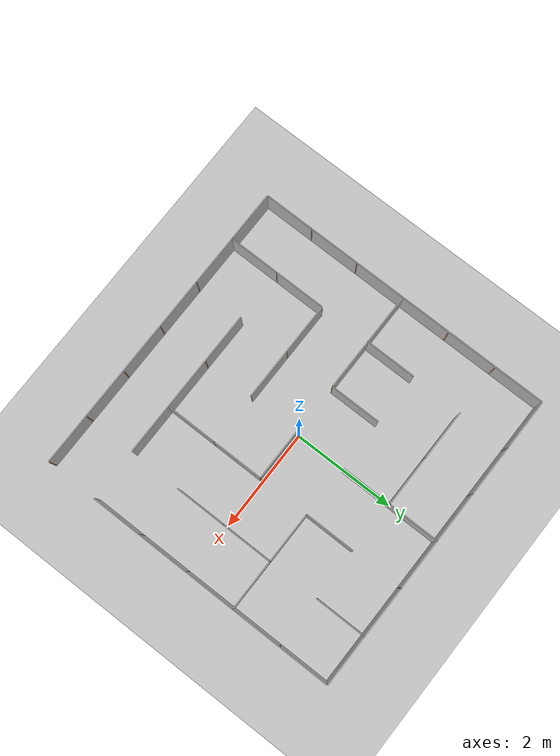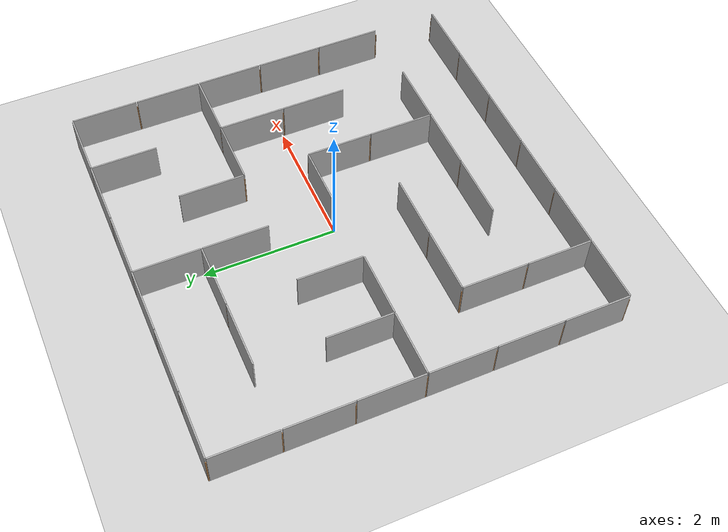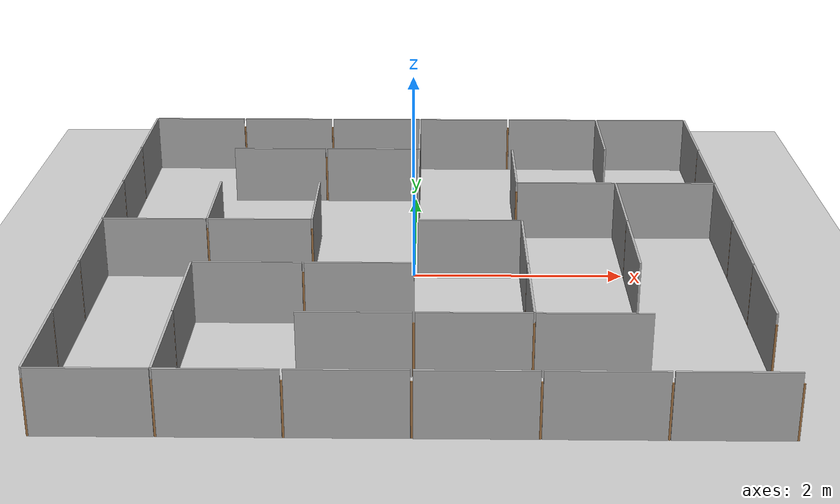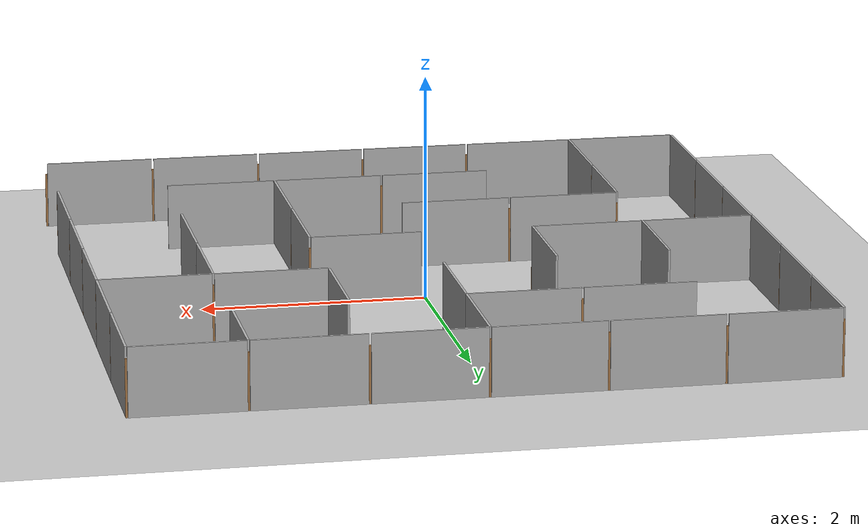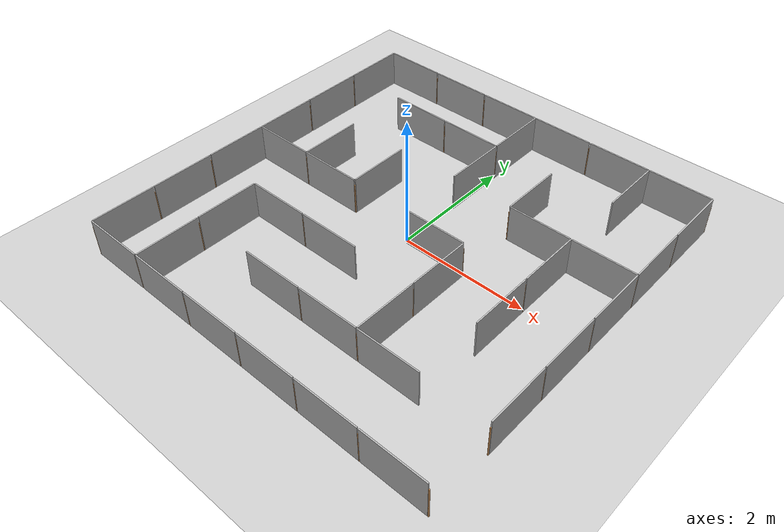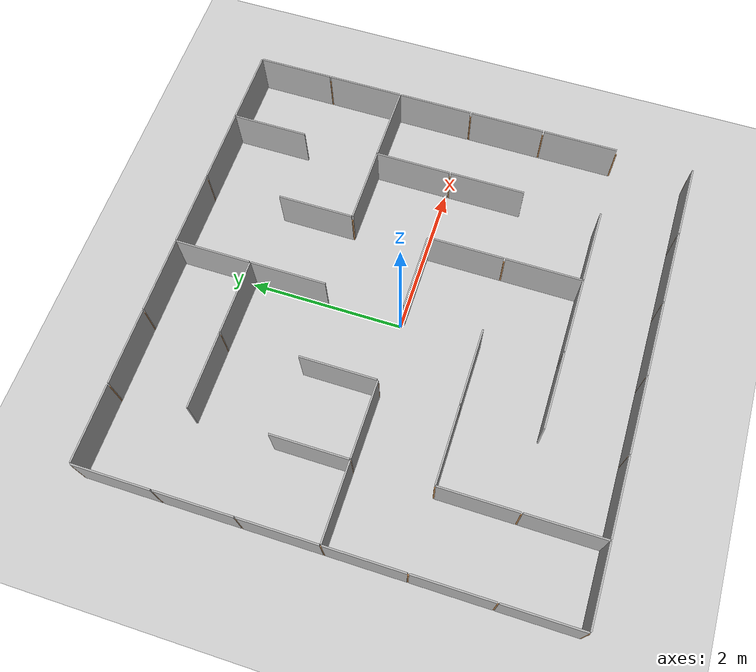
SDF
<sdf version="1.7">
 <world name="default">
  <light name="sun" type="directional">
   <pose>0 0 10 0 -0 0</pose>
   <diffuse>0.8 0.8 0.8 1</diffuse>
   <specular>0.2 0.2 0.2 1</specular>
   <attenuation>
    <range>1000</range>
    <constant>0.9</constant>
    <linear>0.01</linear>
    <quadratic>0.001</quadratic>
   </attenuation>
   <direction>-0.5 0.1 -0.9</direction>
   <spot><inner_angle>0</inner_angle><outer_angle>0</outer_angle><falloff>0</falloff></spot>
  </light>
  <model name="ground_plane">
   <static>1</static>
   <link name="link">
    <collision name="collision">
     <geometry><plane><normal>0 0 1</normal><size>100 100</size></plane></geometry>
     <surface><friction><ode><mu>100</mu><mu2>50</mu2></ode></friction></surface>
    </collision>
    <visual name="visual">
     <cast_shadows>0</cast_shadows>
     <geometry><plane><normal>0 0 1</normal><size>100 100</size></plane></geometry>
     <material>
      <script><uri>file://media/materials/scripts/gazebo.material</uri><name>Gazebo/Grey</name></script>
     </material>
    </visual>
   </link>
  </model>
  <gravity>0 0 -9.8</gravity>
  <magnetic_field>6e-06 2.3e-05 -4.2e-05</magnetic_field>
  <atmosphere type="adiabatic"/>
  <physics type="ode">
   <max_step_size>0.001</max_step_size>
   <real_time_factor>1</real_time_factor>
   <real_time_update_rate>1000</real_time_update_rate>
  </physics>
  <scene><ambient>0.4 0.4 0.4 1</ambient><background>0.7 0.7 0.7 1</background><shadows>1</shadows></scene>
  <audio><device>default</device></audio>
  <spherical_coordinates>
   <surface_model>EARTH_WGS84</surface_model>
   <latitude_deg>0</latitude_deg>
   <longitude_deg>0</longitude_deg>
   <elevation>0</elevation>
   <heading_deg>0</heading_deg>
  </spherical_coordinates>
  <model name="maze_3_6x6">
   <link name="plywood_panel_0_0_b::main">
    <pose>0 0 0 0 -0 1.571</pose>
    <visual name="visual">
     <pose>0.01 -0.01 0 3.14159 -1.57059 3.14159</pose>
     <geometry><mesh><scale>1 1 1</scale><uri>model://plywood_panel/meshes/plywood.dae</uri></mesh></geometry>
     <material><shader type="pixel"/></material>
    </visual>
    <collision name="collision">
     <pose>0 -0.5 0.3 -1.571 -0 -1.571</pose>
     <geometry><box><size>0.98 0.6 0.02</size></box></geometry>
     <surface>
      <friction>
       <ode><mu>1</mu><mu2>1</mu2><fdir1>0 0 0</fdir1><slip1>0</slip1><slip2>0</slip2></ode>
       <torsional>
        <coefficient>1</coefficient>
        <patch_radius>0</patch_radius>
        <surface_radius>0</surface_radius>
        <use_patch_radius>1</use_patch_radius>
        <ode><slip>0</slip></ode>
       </torsional>
      </friction>
      <bounce><restitution_coefficient>0</restitution_coefficient><threshold>1e+06</threshold></bounce>
      <contact>
       <collide_without_contact>0</collide_without_contact>
       <collide_without_contact_bitmask>1</collide_without_contact_bitmask>
       <collide_bitmask>1</collide_bitmask>
       <ode>
        <soft_cfm>0</soft_cfm>
        <soft_erp>0.2</soft_erp>
        <kp>1e+13</kp>
        <kd>1</kd>
        <max_vel>0.01</max_vel>
        <min_depth>0</min_depth>
       </ode>
       <bullet>
        <split_impulse>1</split_impulse>
        <split_impulse_penetration_threshold>-0.01</split_impulse_penetration_threshold>
        <soft_cfm>0</soft_cfm>
        <soft_erp>0.2</soft_erp>
        <kp>1e+13</kp>
        <kd>1</kd>
       </bullet>
      </contact>
     </surface>
    </collision>
   </link>
   <link name="plywood_panel_0_0_a::main">
    <pose>0 0 0 0 -0 3.14159</pose>
    <visual name="visual">
     <pose>0.01 -0.01 0 3.14159 -1.57059 3.14159</pose>
     <geometry><mesh><scale>1 1 1</scale><uri>model://plywood_panel/meshes/plywood.dae</uri></mesh></geometry>
     <material><shader type="pixel"/></material>
    </visual>
    <collision name="collision">
     <pose>0 -0.5 0.3 -1.571 -0 -1.571</pose>
     <geometry><box><size>0.98 0.6 0.02</size></box></geometry>
     <surface>
      <friction>
       <ode><mu>1</mu><mu2>1</mu2><fdir1>0 0 0</fdir1><slip1>0</slip1><slip2>0</slip2></ode>
       <torsional>
        <coefficient>1</coefficient>
        <patch_radius>0</patch_radius>
        <surface_radius>0</surface_radius>
        <use_patch_radius>1</use_patch_radius>
        <ode><slip>0</slip></ode>
       </torsional>
      </friction>
      <bounce><restitution_coefficient>0</restitution_coefficient><threshold>1e+06</threshold></bounce>
      <contact>
       <collide_without_contact>0</collide_without_contact>
       <collide_without_contact_bitmask>1</collide_without_contact_bitmask>
       <collide_bitmask>1</collide_bitmask>
       <ode>
        <soft_cfm>0</soft_cfm>
        <soft_erp>0.2</soft_erp>
        <kp>1e+13</kp>
        <kd>1</kd>
        <max_vel>0.01</max_vel>
        <min_depth>0</min_depth>
       </ode>
       <bullet>
        <split_impulse>1</split_impulse>
        <split_impulse_penetration_threshold>-0.01</split_impulse_penetration_threshold>
        <soft_cfm>0</soft_cfm>
        <soft_erp>0.2</soft_erp>
        <kp>1e+13</kp>
        <kd>1</kd>
       </bullet>
      </contact>
     </surface>
    </collision>
   </link>
   <link name="plywood_panel_0_1_a::main">
    <pose>0 1 0 0 -0 3.14159</pose>
    <visual name="visual">
     <pose>0.01 -0.01 0 3.14159 -1.57059 3.14159</pose>
     <geometry><mesh><scale>1 1 1</scale><uri>model://plywood_panel/meshes/plywood.dae</uri></mesh></geometry>
     <material><shader type="pixel"/></material>
    </visual>
    <collision name="collision">
     <pose>0 -0.5 0.3 -1.571 -0 -1.571</pose>
     <geometry><box><size>0.98 0.6 0.02</size></box></geometry>
     <surface>
      <friction>
       <ode><mu>1</mu><mu2>1</mu2><fdir1>0 0 0</fdir1><slip1>0</slip1><slip2>0</slip2></ode>
       <torsional>
        <coefficient>1</coefficient>
        <patch_radius>0</patch_radius>
        <surface_radius>0</surface_radius>
        <use_patch_radius>1</use_patch_radius>
        <ode><slip>0</slip></ode>
       </torsional>
      </friction>
      <bounce><restitution_coefficient>0</restitution_coefficient><threshold>1e+06</threshold></bounce>
      <contact>
       <collide_without_contact>0</collide_without_contact>
       <collide_without_contact_bitmask>1</collide_without_contact_bitmask>
       <collide_bitmask>1</collide_bitmask>
       <ode>
        <soft_cfm>0</soft_cfm>
        <soft_erp>0.2</soft_erp>
        <kp>1e+13</kp>
        <kd>1</kd>
        <max_vel>0.01</max_vel>
        <min_depth>0</min_depth>
       </ode>
       <bullet>
        <split_impulse>1</split_impulse>
        <split_impulse_penetration_threshold>-0.01</split_impulse_penetration_threshold>
        <soft_cfm>0</soft_cfm>
        <soft_erp>0.2</soft_erp>
        <kp>1e+13</kp>
        <kd>1</kd>
       </bullet>
      </contact>
     </surface>
    </collision>
   </link>
   <link name="plywood_panel_0_2_a::main">
    <pose>0 2 0 0 -0 3.14159</pose>
    <visual name="visual">
     <pose>0.01 -0.01 0 3.14159 -1.57059 3.14159</pose>
     <geometry><mesh><scale>1 1 1</scale><uri>model://plywood_panel/meshes/plywood.dae</uri></mesh></geometry>
     <material><shader type="pixel"/></material>
    </visual>
    <collision name="collision">
     <pose>0 -0.5 0.3 -1.571 -0 -1.571</pose>
     <geometry><box><size>0.98 0.6 0.02</size></box></geometry>
     <surface>
      <friction>
       <ode><mu>1</mu><mu2>1</mu2><fdir1>0 0 0</fdir1><slip1>0</slip1><slip2>0</slip2></ode>
       <torsional>
        <coefficient>1</coefficient>
        <patch_radius>0</patch_radius>
        <surface_radius>0</surface_radius>
        <use_patch_radius>1</use_patch_radius>
        <ode><slip>0</slip></ode>
       </torsional>
      </friction>
      <bounce><restitution_coefficient>0</restitution_coefficient><threshold>1e+06</threshold></bounce>
      <contact>
       <collide_without_contact>0</collide_without_contact>
       <collide_without_contact_bitmask>1</collide_without_contact_bitmask>
       <collide_bitmask>1</collide_bitmask>
       <ode>
        <soft_cfm>0</soft_cfm>
        <soft_erp>0.2</soft_erp>
        <kp>1e+13</kp>
        <kd>1</kd>
        <max_vel>0.01</max_vel>
        <min_depth>0</min_depth>
       </ode>
       <bullet>
        <split_impulse>1</split_impulse>
        <split_impulse_penetration_threshold>-0.01</split_impulse_penetration_threshold>
        <soft_cfm>0</soft_cfm>
        <soft_erp>0.2</soft_erp>
        <kp>1e+13</kp>
        <kd>1</kd>
       </bullet>
      </contact>
     </surface>
    </collision>
   </link>
   <link name="plywood_panel_0_3_a::main">
    <pose>0 3 0 0 -0 3.14159</pose>
    <visual name="visual">
     <pose>0.01 -0.01 0 3.14159 -1.57059 3.14159</pose>
     <geometry><mesh><scale>1 1 1</scale><uri>model://plywood_panel/meshes/plywood.dae</uri></mesh></geometry>
     <material><shader type="pixel"/></material>
    </visual>
    <collision name="collision">
     <pose>0 -0.5 0.3 -1.571 -0 -1.571</pose>
     <geometry><box><size>0.98 0.6 0.02</size></box></geometry>
     <surface>
      <friction>
       <ode><mu>1</mu><mu2>1</mu2><fdir1>0 0 0</fdir1><slip1>0</slip1><slip2>0</slip2></ode>
       <torsional>
        <coefficient>1</coefficient>
        <patch_radius>0</patch_radius>
        <surface_radius>0</surface_radius>
        <use_patch_radius>1</use_patch_radius>
        <ode><slip>0</slip></ode>
       </torsional>
      </friction>
      <bounce><restitution_coefficient>0</restitution_coefficient><threshold>1e+06</threshold></bounce>
      <contact>
       <collide_without_contact>0</collide_without_contact>
       <collide_without_contact_bitmask>1</collide_without_contact_bitmask>
       <collide_bitmask>1</collide_bitmask>
       <ode>
        <soft_cfm>0</soft_cfm>
        <soft_erp>0.2</soft_erp>
        <kp>1e+13</kp>
        <kd>1</kd>
        <max_vel>0.01</max_vel>
        <min_depth>0</min_depth>
       </ode>
       <bullet>
        <split_impulse>1</split_impulse>
        <split_impulse_penetration_threshold>-0.01</split_impulse_penetration_threshold>
        <soft_cfm>0</soft_cfm>
        <soft_erp>0.2</soft_erp>
        <kp>1e+13</kp>
        <kd>1</kd>
       </bullet>
      </contact>
     </surface>
    </collision>
   </link>
   <link name="plywood_panel_0_4_a::main">
    <pose>0 4 0 0 -0 3.14159</pose>
    <visual name="visual">
     <pose>0.01 -0.01 0 3.14159 -1.57059 3.14159</pose>
     <geometry><mesh><scale>1 1 1</scale><uri>model://plywood_panel/meshes/plywood.dae</uri></mesh></geometry>
     <material><shader type="pixel"/></material>
    </visual>
    <collision name="collision">
     <pose>0 -0.5 0.3 -1.571 -0 -1.571</pose>
     <geometry><box><size>0.98 0.6 0.02</size></box></geometry>
     <surface>
      <friction>
       <ode><mu>1</mu><mu2>1</mu2><fdir1>0 0 0</fdir1><slip1>0</slip1><slip2>0</slip2></ode>
       <torsional>
        <coefficient>1</coefficient>
        <patch_radius>0</patch_radius>
        <surface_radius>0</surface_radius>
        <use_patch_radius>1</use_patch_radius>
        <ode><slip>0</slip></ode>
       </torsional>
      </friction>
      <bounce><restitution_coefficient>0</restitution_coefficient><threshold>1e+06</threshold></bounce>
      <contact>
       <collide_without_contact>0</collide_without_contact>
       <collide_without_contact_bitmask>1</collide_without_contact_bitmask>
       <collide_bitmask>1</collide_bitmask>
       <ode>
        <soft_cfm>0</soft_cfm>
        <soft_erp>0.2</soft_erp>
        <kp>1e+13</kp>
        <kd>1</kd>
        <max_vel>0.01</max_vel>
        <min_depth>0</min_depth>
       </ode>
       <bullet>
        <split_impulse>1</split_impulse>
        <split_impulse_penetration_threshold>-0.01</split_impulse_penetration_threshold>
        <soft_cfm>0</soft_cfm>
        <soft_erp>0.2</soft_erp>
        <kp>1e+13</kp>
        <kd>1</kd>
       </bullet>
      </contact>
     </surface>
    </collision>
   </link>
   <link name="plywood_panel_0_6_b::main">
    <pose>0 6 0 0 -0 1.571</pose>
    <visual name="visual">
     <pose>0.01 -0.01 0 3.14159 -1.57059 3.14159</pose>
     <geometry><mesh><scale>1 1 1</scale><uri>model://plywood_panel/meshes/plywood.dae</uri></mesh></geometry>
     <material><shader type="pixel"/></material>
    </visual>
    <collision name="collision">
     <pose>0 -0.5 0.3 -1.571 -0 -1.571</pose>
     <geometry><box><size>0.98 0.6 0.02</size></box></geometry>
     <surface>
      <friction>
       <ode><mu>1</mu><mu2>1</mu2><fdir1>0 0 0</fdir1><slip1>0</slip1><slip2>0</slip2></ode>
       <torsional>
        <coefficient>1</coefficient>
        <patch_radius>0</patch_radius>
        <surface_radius>0</surface_radius>
        <use_patch_radius>1</use_patch_radius>
        <ode><slip>0</slip></ode>
       </torsional>
      </friction>
      <bounce><restitution_coefficient>0</restitution_coefficient><threshold>1e+06</threshold></bounce>
      <contact>
       <collide_without_contact>0</collide_without_contact>
       <collide_without_contact_bitmask>1</collide_without_contact_bitmask>
       <collide_bitmask>1</collide_bitmask>
       <ode>
        <soft_cfm>0</soft_cfm>
        <soft_erp>0.2</soft_erp>
        <kp>1e+13</kp>
        <kd>1</kd>
        <max_vel>0.01</max_vel>
        <min_depth>0</min_depth>
       </ode>
       <bullet>
        <split_impulse>1</split_impulse>
        <split_impulse_penetration_threshold>-0.01</split_impulse_penetration_threshold>
        <soft_cfm>0</soft_cfm>
        <soft_erp>0.2</soft_erp>
        <kp>1e+13</kp>
        <kd>1</kd>
       </bullet>
      </contact>
     </surface>
    </collision>
   </link>
   <link name="plywood_panel_1_0_b::main">
    <pose>1 0 0 0 -0 1.571</pose>
    <visual name="visual">
     <pose>0.01 -0.01 0 3.14159 -1.57059 3.14159</pose>
     <geometry><mesh><scale>1 1 1</scale><uri>model://plywood_panel/meshes/plywood.dae</uri></mesh></geometry>
     <material><shader type="pixel"/></material>
    </visual>
    <collision name="collision">
     <pose>0 -0.5 0.3 -1.571 -0 -1.571</pose>
     <geometry><box><size>0.98 0.6 0.02</size></box></geometry>
     <surface>
      <friction>
       <ode><mu>1</mu><mu2>1</mu2><fdir1>0 0 0</fdir1><slip1>0</slip1><slip2>0</slip2></ode>
       <torsional>
        <coefficient>1</coefficient>
        <patch_radius>0</patch_radius>
        <surface_radius>0</surface_radius>
        <use_patch_radius>1</use_patch_radius>
        <ode><slip>0</slip></ode>
       </torsional>
      </friction>
      <bounce><restitution_coefficient>0</restitution_coefficient><threshold>1e+06</threshold></bounce>
      <contact>
       <collide_without_contact>0</collide_without_contact>
       <collide_without_contact_bitmask>1</collide_without_contact_bitmask>
       <collide_bitmask>1</collide_bitmask>
       <ode>
        <soft_cfm>0</soft_cfm>
        <soft_erp>0.2</soft_erp>
        <kp>1e+13</kp>
        <kd>1</kd>
        <max_vel>0.01</max_vel>
        <min_depth>0</min_depth>
       </ode>
       <bullet>
        <split_impulse>1</split_impulse>
        <split_impulse_penetration_threshold>-0.01</split_impulse_penetration_threshold>
        <soft_cfm>0</soft_cfm>
        <soft_erp>0.2</soft_erp>
        <kp>1e+13</kp>
        <kd>1</kd>
       </bullet>
      </contact>
     </surface>
    </collision>
   </link>
   <link name="plywood_panel_1_1_a::main">
    <pose>1 1 0 0 -0 0</pose>
    <visual name="visual">
     <pose>0.01 -0.01 0 3.14159 -1.57059 3.14159</pose>
     <geometry><mesh><scale>1 1 1</scale><uri>model://plywood_panel/meshes/plywood.dae</uri></mesh></geometry>
     <material><shader type="pixel"/></material>
    </visual>
    <collision name="collision">
     <pose>0 -0.5 0.3 -1.571 -0 -1.571</pose>
     <geometry><box><size>0.98 0.6 0.02</size></box></geometry>
     <surface>
      <friction>
       <ode><mu>1</mu><mu2>1</mu2><fdir1>0 0 0</fdir1><slip1>0</slip1><slip2>0</slip2></ode>
       <torsional>
        <coefficient>1</coefficient>
        <patch_radius>0</patch_radius>
        <surface_radius>0</surface_radius>
        <use_patch_radius>1</use_patch_radius>
        <ode><slip>0</slip></ode>
       </torsional>
      </friction>
      <bounce><restitution_coefficient>0</restitution_coefficient><threshold>1e+06</threshold></bounce>
      <contact>
       <collide_without_contact>0</collide_without_contact>
       <collide_without_contact_bitmask>1</collide_without_contact_bitmask>
       <collide_bitmask>1</collide_bitmask>
       <ode>
        <soft_cfm>0</soft_cfm>
        <soft_erp>0.2</soft_erp>
        <kp>1e+13</kp>
        <kd>1</kd>
        <max_vel>0.01</max_vel>
        <min_depth>0</min_depth>
       </ode>
       <bullet>
        <split_impulse>1</split_impulse>
        <split_impulse_penetration_threshold>-0.01</split_impulse_penetration_threshold>
        <soft_cfm>0</soft_cfm>
        <soft_erp>0.2</soft_erp>
        <kp>1e+13</kp>
        <kd>1</kd>
       </bullet>
      </contact>
     </surface>
    </collision>
   </link>
   <link name="plywood_panel_1_2_c::main">
    <pose>1 2 0 0 0 -1.5708</pose>
    <visual name="visual">
     <pose>0.01 -0.01 0 3.14159 -1.57059 3.14159</pose>
     <geometry><mesh><scale>1 1 1</scale><uri>model://plywood_panel/meshes/plywood.dae</uri></mesh></geometry>
     <material><shader type="pixel"/></material>
    </visual>
    <collision name="collision">
     <pose>0 -0.5 0.3 -1.571 -0 -1.571</pose>
     <geometry><box><size>0.98 0.6 0.02</size></box></geometry>
     <surface>
      <friction>
       <ode><mu>1</mu><mu2>1</mu2><fdir1>0 0 0</fdir1><slip1>0</slip1><slip2>0</slip2></ode>
       <torsional>
        <coefficient>1</coefficient>
        <patch_radius>0</patch_radius>
        <surface_radius>0</surface_radius>
        <use_patch_radius>1</use_patch_radius>
        <ode><slip>0</slip></ode>
       </torsional>
      </friction>
      <bounce><restitution_coefficient>0</restitution_coefficient><threshold>1e+06</threshold></bounce>
      <contact>
       <collide_without_contact>0</collide_without_contact>
       <collide_without_contact_bitmask>1</collide_without_contact_bitmask>
       <collide_bitmask>1</collide_bitmask>
       <ode>
        <soft_cfm>0</soft_cfm>
        <soft_erp>0.2</soft_erp>
        <kp>1e+13</kp>
        <kd>1</kd>
        <max_vel>0.01</max_vel>
        <min_depth>0</min_depth>
       </ode>
       <bullet>
        <split_impulse>1</split_impulse>
        <split_impulse_penetration_threshold>-0.01</split_impulse_penetration_threshold>
        <soft_cfm>0</soft_cfm>
        <soft_erp>0.2</soft_erp>
        <kp>1e+13</kp>
        <kd>1</kd>
       </bullet>
      </contact>
     </surface>
    </collision>
   </link>
   <link name="plywood_panel_1_3_a::main">
    <pose>1 3 0 0 -0 0</pose>
    <visual name="visual">
     <pose>0.01 -0.01 0 3.14159 -1.57059 3.14159</pose>
     <geometry><mesh><scale>1 1 1</scale><uri>model://plywood_panel/meshes/plywood.dae</uri></mesh></geometry>
     <material><shader type="pixel"/></material>
    </visual>
    <collision name="collision">
     <pose>0 -0.5 0.3 -1.571 -0 -1.571</pose>
     <geometry><box><size>0.98 0.6 0.02</size></box></geometry>
     <surface>
      <friction>
       <ode><mu>1</mu><mu2>1</mu2><fdir1>0 0 0</fdir1><slip1>0</slip1><slip2>0</slip2></ode>
       <torsional>
        <coefficient>1</coefficient>
        <patch_radius>0</patch_radius>
        <surface_radius>0</surface_radius>
        <use_patch_radius>1</use_patch_radius>
        <ode><slip>0</slip></ode>
       </torsional>
      </friction>
      <bounce><restitution_coefficient>0</restitution_coefficient><threshold>1e+06</threshold></bounce>
      <contact>
       <collide_without_contact>0</collide_without_contact>
       <collide_without_contact_bitmask>1</collide_without_contact_bitmask>
       <collide_bitmask>1</collide_bitmask>
       <ode>
        <soft_cfm>0</soft_cfm>
        <soft_erp>0.2</soft_erp>
        <kp>1e+13</kp>
        <kd>1</kd>
        <max_vel>0.01</max_vel>
        <min_depth>0</min_depth>
       </ode>
       <bullet>
        <split_impulse>1</split_impulse>
        <split_impulse_penetration_threshold>-0.01</split_impulse_penetration_threshold>
        <soft_cfm>0</soft_cfm>
        <soft_erp>0.2</soft_erp>
        <kp>1e+13</kp>
        <kd>1</kd>
       </bullet>
      </contact>
     </surface>
    </collision>
   </link>
   <link name="plywood_panel_1_4_a::main">
    <pose>1 4 0 0 -0 0</pose>
    <visual name="visual">
     <pose>0.01 -0.01 0 3.14159 -1.57059 3.14159</pose>
     <geometry><mesh><scale>1 1 1</scale><uri>model://plywood_panel/meshes/plywood.dae</uri></mesh></geometry>
     <material><shader type="pixel"/></material>
    </visual>
    <collision name="collision">
     <pose>0 -0.5 0.3 -1.571 -0 -1.571</pose>
     <geometry><box><size>0.98 0.6 0.02</size></box></geometry>
     <surface>
      <friction>
       <ode><mu>1</mu><mu2>1</mu2><fdir1>0 0 0</fdir1><slip1>0</slip1><slip2>0</slip2></ode>
       <torsional>
        <coefficient>1</coefficient>
        <patch_radius>0</patch_radius>
        <surface_radius>0</surface_radius>
        <use_patch_radius>1</use_patch_radius>
        <ode><slip>0</slip></ode>
       </torsional>
      </friction>
      <bounce><restitution_coefficient>0</restitution_coefficient><threshold>1e+06</threshold></bounce>
      <contact>
       <collide_without_contact>0</collide_without_contact>
       <collide_without_contact_bitmask>1</collide_without_contact_bitmask>
       <collide_bitmask>1</collide_bitmask>
       <ode>
        <soft_cfm>0</soft_cfm>
        <soft_erp>0.2</soft_erp>
        <kp>1e+13</kp>
        <kd>1</kd>
        <max_vel>0.01</max_vel>
        <min_depth>0</min_depth>
       </ode>
       <bullet>
        <split_impulse>1</split_impulse>
        <split_impulse_penetration_threshold>-0.01</split_impulse_penetration_threshold>
        <soft_cfm>0</soft_cfm>
        <soft_erp>0.2</soft_erp>
        <kp>1e+13</kp>
        <kd>1</kd>
       </bullet>
      </contact>
     </surface>
    </collision>
   </link>
   <link name="plywood_panel_1_6_b::main">
    <pose>1 6 0 0 -0 1.571</pose>
    <visual name="visual">
     <pose>0.01 -0.01 0 3.14159 -1.57059 3.14159</pose>
     <geometry><mesh><scale>1 1 1</scale><uri>model://plywood_panel/meshes/plywood.dae</uri></mesh></geometry>
     <material><shader type="pixel"/></material>
    </visual>
    <collision name="collision">
     <pose>0 -0.5 0.3 -1.571 -0 -1.571</pose>
     <geometry><box><size>0.98 0.6 0.02</size></box></geometry>
     <surface>
      <friction>
       <ode><mu>1</mu><mu2>1</mu2><fdir1>0 0 0</fdir1><slip1>0</slip1><slip2>0</slip2></ode>
       <torsional>
        <coefficient>1</coefficient>
        <patch_radius>0</patch_radius>
        <surface_radius>0</surface_radius>
        <use_patch_radius>1</use_patch_radius>
        <ode><slip>0</slip></ode>
       </torsional>
      </friction>
      <bounce><restitution_coefficient>0</restitution_coefficient><threshold>1e+06</threshold></bounce>
      <contact>
       <collide_without_contact>0</collide_without_contact>
       <collide_without_contact_bitmask>1</collide_without_contact_bitmask>
       <collide_bitmask>1</collide_bitmask>
       <ode>
        <soft_cfm>0</soft_cfm>
        <soft_erp>0.2</soft_erp>
        <kp>1e+13</kp>
        <kd>1</kd>
        <max_vel>0.01</max_vel>
        <min_depth>0</min_depth>
       </ode>
       <bullet>
        <split_impulse>1</split_impulse>
        <split_impulse_penetration_threshold>-0.01</split_impulse_penetration_threshold>
        <soft_cfm>0</soft_cfm>
        <soft_erp>0.2</soft_erp>
        <kp>1e+13</kp>
        <kd>1</kd>
       </bullet>
      </contact>
     </surface>
    </collision>
   </link>
   <link name="plywood_panel_2_0_b::main">
    <pose>2 0 0 0 -0 1.571</pose>
    <visual name="visual">
     <pose>0.01 -0.01 0 3.14159 -1.57059 3.14159</pose>
     <geometry><mesh><scale>1 1 1</scale><uri>model://plywood_panel/meshes/plywood.dae</uri></mesh></geometry>
     <material><shader type="pixel"/></material>
    </visual>
    <collision name="collision">
     <pose>0 -0.5 0.3 -1.571 -0 -1.571</pose>
     <geometry><box><size>0.98 0.6 0.02</size></box></geometry>
     <surface>
      <friction>
       <ode><mu>1</mu><mu2>1</mu2><fdir1>0 0 0</fdir1><slip1>0</slip1><slip2>0</slip2></ode>
       <torsional>
        <coefficient>1</coefficient>
        <patch_radius>0</patch_radius>
        <surface_radius>0</surface_radius>
        <use_patch_radius>1</use_patch_radius>
        <ode><slip>0</slip></ode>
       </torsional>
      </friction>
      <bounce><restitution_coefficient>0</restitution_coefficient><threshold>1e+06</threshold></bounce>
      <contact>
       <collide_without_contact>0</collide_without_contact>
       <collide_without_contact_bitmask>1</collide_without_contact_bitmask>
       <collide_bitmask>1</collide_bitmask>
       <ode>
        <soft_cfm>0</soft_cfm>
        <soft_erp>0.2</soft_erp>
        <kp>1e+13</kp>
        <kd>1</kd>
        <max_vel>0.01</max_vel>
        <min_depth>0</min_depth>
       </ode>
       <bullet>
        <split_impulse>1</split_impulse>
        <split_impulse_penetration_threshold>-0.01</split_impulse_penetration_threshold>
        <soft_cfm>0</soft_cfm>
        <soft_erp>0.2</soft_erp>
        <kp>1e+13</kp>
        <kd>1</kd>
       </bullet>
      </contact>
     </surface>
    </collision>
   </link>
   <link name="plywood_panel_2_2_a::main">
    <pose>2 2 0 0 -0 0</pose>
    <visual name="visual">
     <pose>0.01 -0.01 0 3.14159 -1.57059 3.14159</pose>
     <geometry><mesh><scale>1 1 1</scale><uri>model://plywood_panel/meshes/plywood.dae</uri></mesh></geometry>
     <material><shader type="pixel"/></material>
    </visual>
    <collision name="collision">
     <pose>0 -0.5 0.3 -1.571 -0 -1.571</pose>
     <geometry><box><size>0.98 0.6 0.02</size></box></geometry>
     <surface>
      <friction>
       <ode><mu>1</mu><mu2>1</mu2><fdir1>0 0 0</fdir1><slip1>0</slip1><slip2>0</slip2></ode>
       <torsional>
        <coefficient>1</coefficient>
        <patch_radius>0</patch_radius>
        <surface_radius>0</surface_radius>
        <use_patch_radius>1</use_patch_radius>
        <ode><slip>0</slip></ode>
       </torsional>
      </friction>
      <bounce><restitution_coefficient>0</restitution_coefficient><threshold>1e+06</threshold></bounce>
      <contact>
       <collide_without_contact>0</collide_without_contact>
       <collide_without_contact_bitmask>1</collide_without_contact_bitmask>
       <collide_bitmask>1</collide_bitmask>
       <ode>
        <soft_cfm>0</soft_cfm>
        <soft_erp>0.2</soft_erp>
        <kp>1e+13</kp>
        <kd>1</kd>
        <max_vel>0.01</max_vel>
        <min_depth>0</min_depth>
       </ode>
       <bullet>
        <split_impulse>1</split_impulse>
        <split_impulse_penetration_threshold>-0.01</split_impulse_penetration_threshold>
        <soft_cfm>0</soft_cfm>
        <soft_erp>0.2</soft_erp>
        <kp>1e+13</kp>
        <kd>1</kd>
       </bullet>
      </contact>
     </surface>
    </collision>
   </link>
   <link name="plywood_panel_2_2_c::main">
    <pose>2 2 0 0 0 -1.5708</pose>
    <visual name="visual">
     <pose>0.01 -0.01 0 3.14159 -1.57059 3.14159</pose>
     <geometry><mesh><scale>1 1 1</scale><uri>model://plywood_panel/meshes/plywood.dae</uri></mesh></geometry>
     <material><shader type="pixel"/></material>
    </visual>
    <collision name="collision">
     <pose>0 -0.5 0.3 -1.571 -0 -1.571</pose>
     <geometry><box><size>0.98 0.6 0.02</size></box></geometry>
     <surface>
      <friction>
       <ode><mu>1</mu><mu2>1</mu2><fdir1>0 0 0</fdir1><slip1>0</slip1><slip2>0</slip2></ode>
       <torsional>
        <coefficient>1</coefficient>
        <patch_radius>0</patch_radius>
        <surface_radius>0</surface_radius>
        <use_patch_radius>1</use_patch_radius>
        <ode><slip>0</slip></ode>
       </torsional>
      </friction>
      <bounce><restitution_coefficient>0</restitution_coefficient><threshold>1e+06</threshold></bounce>
      <contact>
       <collide_without_contact>0</collide_without_contact>
       <collide_without_contact_bitmask>1</collide_without_contact_bitmask>
       <collide_bitmask>1</collide_bitmask>
       <ode>
        <soft_cfm>0</soft_cfm>
        <soft_erp>0.2</soft_erp>
        <kp>1e+13</kp>
        <kd>1</kd>
        <max_vel>0.01</max_vel>
        <min_depth>0</min_depth>
       </ode>
       <bullet>
        <split_impulse>1</split_impulse>
        <split_impulse_penetration_threshold>-0.01</split_impulse_penetration_threshold>
        <soft_cfm>0</soft_cfm>
        <soft_erp>0.2</soft_erp>
        <kp>1e+13</kp>
        <kd>1</kd>
       </bullet>
      </contact>
     </surface>
    </collision>
   </link>
   <link name="plywood_panel_2_4_a::main">
    <pose>2 4 0 0 -0 0</pose>
    <visual name="visual">
     <pose>0.01 -0.01 0 3.14159 -1.57059 3.14159</pose>
     <geometry><mesh><scale>1 1 1</scale><uri>model://plywood_panel/meshes/plywood.dae</uri></mesh></geometry>
     <material><shader type="pixel"/></material>
    </visual>
    <collision name="collision">
     <pose>0 -0.5 0.3 -1.571 -0 -1.571</pose>
     <geometry><box><size>0.98 0.6 0.02</size></box></geometry>
     <surface>
      <friction>
       <ode><mu>1</mu><mu2>1</mu2><fdir1>0 0 0</fdir1><slip1>0</slip1><slip2>0</slip2></ode>
       <torsional>
        <coefficient>1</coefficient>
        <patch_radius>0</patch_radius>
        <surface_radius>0</surface_radius>
        <use_patch_radius>1</use_patch_radius>
        <ode><slip>0</slip></ode>
       </torsional>
      </friction>
      <bounce><restitution_coefficient>0</restitution_coefficient><threshold>1e+06</threshold></bounce>
      <contact>
       <collide_without_contact>0</collide_without_contact>
       <collide_without_contact_bitmask>1</collide_without_contact_bitmask>
       <collide_bitmask>1</collide_bitmask>
       <ode>
        <soft_cfm>0</soft_cfm>
        <soft_erp>0.2</soft_erp>
        <kp>1e+13</kp>
        <kd>1</kd>
        <max_vel>0.01</max_vel>
        <min_depth>0</min_depth>
       </ode>
       <bullet>
        <split_impulse>1</split_impulse>
        <split_impulse_penetration_threshold>-0.01</split_impulse_penetration_threshold>
        <soft_cfm>0</soft_cfm>
        <soft_erp>0.2</soft_erp>
        <kp>1e+13</kp>
        <kd>1</kd>
       </bullet>
      </contact>
     </surface>
    </collision>
   </link>
   <link name="plywood_panel_2_5_a::main">
    <pose>2 5 0 0 -0 0</pose>
    <visual name="visual">
     <pose>0.01 -0.01 0 3.14159 -1.57059 3.14159</pose>
     <geometry><mesh><scale>1 1 1</scale><uri>model://plywood_panel/meshes/plywood.dae</uri></mesh></geometry>
     <material><shader type="pixel"/></material>
    </visual>
    <collision name="collision">
     <pose>0 -0.5 0.3 -1.571 -0 -1.571</pose>
     <geometry><box><size>0.98 0.6 0.02</size></box></geometry>
     <surface>
      <friction>
       <ode><mu>1</mu><mu2>1</mu2><fdir1>0 0 0</fdir1><slip1>0</slip1><slip2>0</slip2></ode>
       <torsional>
        <coefficient>1</coefficient>
        <patch_radius>0</patch_radius>
        <surface_radius>0</surface_radius>
        <use_patch_radius>1</use_patch_radius>
        <ode><slip>0</slip></ode>
       </torsional>
      </friction>
      <bounce><restitution_coefficient>0</restitution_coefficient><threshold>1e+06</threshold></bounce>
      <contact>
       <collide_without_contact>0</collide_without_contact>
       <collide_without_contact_bitmask>1</collide_without_contact_bitmask>
       <collide_bitmask>1</collide_bitmask>
       <ode>
        <soft_cfm>0</soft_cfm>
        <soft_erp>0.2</soft_erp>
        <kp>1e+13</kp>
        <kd>1</kd>
        <max_vel>0.01</max_vel>
        <min_depth>0</min_depth>
       </ode>
       <bullet>
        <split_impulse>1</split_impulse>
        <split_impulse_penetration_threshold>-0.01</split_impulse_penetration_threshold>
        <soft_cfm>0</soft_cfm>
        <soft_erp>0.2</soft_erp>
        <kp>1e+13</kp>
        <kd>1</kd>
       </bullet>
      </contact>
     </surface>
    </collision>
   </link>
   <link name="plywood_panel_2_5_c::main">
    <pose>2 5 0 0 0 -1.5708</pose>
    <visual name="visual">
     <pose>0.01 -0.01 0 3.14159 -1.57059 3.14159</pose>
     <geometry><mesh><scale>1 1 1</scale><uri>model://plywood_panel/meshes/plywood.dae</uri></mesh></geometry>
     <material><shader type="pixel"/></material>
    </visual>
    <collision name="collision">
     <pose>0 -0.5 0.3 -1.571 -0 -1.571</pose>
     <geometry><box><size>0.98 0.6 0.02</size></box></geometry>
     <surface>
      <friction>
       <ode><mu>1</mu><mu2>1</mu2><fdir1>0 0 0</fdir1><slip1>0</slip1><slip2>0</slip2></ode>
       <torsional>
        <coefficient>1</coefficient>
        <patch_radius>0</patch_radius>
        <surface_radius>0</surface_radius>
        <use_patch_radius>1</use_patch_radius>
        <ode><slip>0</slip></ode>
       </torsional>
      </friction>
      <bounce><restitution_coefficient>0</restitution_coefficient><threshold>1e+06</threshold></bounce>
      <contact>
       <collide_without_contact>0</collide_without_contact>
       <collide_without_contact_bitmask>1</collide_without_contact_bitmask>
       <collide_bitmask>1</collide_bitmask>
       <ode>
        <soft_cfm>0</soft_cfm>
        <soft_erp>0.2</soft_erp>
        <kp>1e+13</kp>
        <kd>1</kd>
        <max_vel>0.01</max_vel>
        <min_depth>0</min_depth>
       </ode>
       <bullet>
        <split_impulse>1</split_impulse>
        <split_impulse_penetration_threshold>-0.01</split_impulse_penetration_threshold>
        <soft_cfm>0</soft_cfm>
        <soft_erp>0.2</soft_erp>
        <kp>1e+13</kp>
        <kd>1</kd>
       </bullet>
      </contact>
     </surface>
    </collision>
   </link>
   <link name="plywood_panel_2_6_b::main">
    <pose>2 6 0 0 -0 1.571</pose>
    <visual name="visual">
     <pose>0.01 -0.01 0 3.14159 -1.57059 3.14159</pose>
     <geometry><mesh><scale>1 1 1</scale><uri>model://plywood_panel/meshes/plywood.dae</uri></mesh></geometry>
     <material><shader type="pixel"/></material>
    </visual>
    <collision name="collision">
     <pose>0 -0.5 0.3 -1.571 -0 -1.571</pose>
     <geometry><box><size>0.98 0.6 0.02</size></box></geometry>
     <surface>
      <friction>
       <ode><mu>1</mu><mu2>1</mu2><fdir1>0 0 0</fdir1><slip1>0</slip1><slip2>0</slip2></ode>
       <torsional>
        <coefficient>1</coefficient>
        <patch_radius>0</patch_radius>
        <surface_radius>0</surface_radius>
        <use_patch_radius>1</use_patch_radius>
        <ode><slip>0</slip></ode>
       </torsional>
      </friction>
      <bounce><restitution_coefficient>0</restitution_coefficient><threshold>1e+06</threshold></bounce>
      <contact>
       <collide_without_contact>0</collide_without_contact>
       <collide_without_contact_bitmask>1</collide_without_contact_bitmask>
       <collide_bitmask>1</collide_bitmask>
       <ode>
        <soft_cfm>0</soft_cfm>
        <soft_erp>0.2</soft_erp>
        <kp>1e+13</kp>
        <kd>1</kd>
        <max_vel>0.01</max_vel>
        <min_depth>0</min_depth>
       </ode>
       <bullet>
        <split_impulse>1</split_impulse>
        <split_impulse_penetration_threshold>-0.01</split_impulse_penetration_threshold>
        <soft_cfm>0</soft_cfm>
        <soft_erp>0.2</soft_erp>
        <kp>1e+13</kp>
        <kd>1</kd>
       </bullet>
      </contact>
     </surface>
    </collision>
   </link>
   <link name="plywood_panel_3_0_b::main">
    <pose>3 0 0 0 -0 1.571</pose>
    <visual name="visual">
     <pose>0.01 -0.01 0 3.14159 -1.57059 3.14159</pose>
     <geometry><mesh><scale>1 1 1</scale><uri>model://plywood_panel/meshes/plywood.dae</uri></mesh></geometry>
     <material><shader type="pixel"/></material>
    </visual>
    <collision name="collision">
     <pose>0 -0.5 0.3 -1.571 -0 -1.571</pose>
     <geometry><box><size>0.98 0.6 0.02</size></box></geometry>
     <surface>
      <friction>
       <ode><mu>1</mu><mu2>1</mu2><fdir1>0 0 0</fdir1><slip1>0</slip1><slip2>0</slip2></ode>
       <torsional>
        <coefficient>1</coefficient>
        <patch_radius>0</patch_radius>
        <surface_radius>0</surface_radius>
        <use_patch_radius>1</use_patch_radius>
        <ode><slip>0</slip></ode>
       </torsional>
      </friction>
      <bounce><restitution_coefficient>0</restitution_coefficient><threshold>1e+06</threshold></bounce>
      <contact>
       <collide_without_contact>0</collide_without_contact>
       <collide_without_contact_bitmask>1</collide_without_contact_bitmask>
       <collide_bitmask>1</collide_bitmask>
       <ode>
        <soft_cfm>0</soft_cfm>
        <soft_erp>0.2</soft_erp>
        <kp>1e+13</kp>
        <kd>1</kd>
        <max_vel>0.01</max_vel>
        <min_depth>0</min_depth>
       </ode>
       <bullet>
        <split_impulse>1</split_impulse>
        <split_impulse_penetration_threshold>-0.01</split_impulse_penetration_threshold>
        <soft_cfm>0</soft_cfm>
        <soft_erp>0.2</soft_erp>
        <kp>1e+13</kp>
        <kd>1</kd>
       </bullet>
      </contact>
     </surface>
    </collision>
   </link>
   <link name="plywood_panel_3_1_a::main">
    <pose>3 1 0 0 -0 0</pose>
    <visual name="visual">
     <pose>0.01 -0.01 0 3.14159 -1.57059 3.14159</pose>
     <geometry><mesh><scale>1 1 1</scale><uri>model://plywood_panel/meshes/plywood.dae</uri></mesh></geometry>
     <material><shader type="pixel"/></material>
    </visual>
    <collision name="collision">
     <pose>0 -0.5 0.3 -1.571 -0 -1.571</pose>
     <geometry><box><size>0.98 0.6 0.02</size></box></geometry>
     <surface>
      <friction>
       <ode><mu>1</mu><mu2>1</mu2><fdir1>0 0 0</fdir1><slip1>0</slip1><slip2>0</slip2></ode>
       <torsional>
        <coefficient>1</coefficient>
        <patch_radius>0</patch_radius>
        <surface_radius>0</surface_radius>
        <use_patch_radius>1</use_patch_radius>
        <ode><slip>0</slip></ode>
       </torsional>
      </friction>
      <bounce><restitution_coefficient>0</restitution_coefficient><threshold>1e+06</threshold></bounce>
      <contact>
       <collide_without_contact>0</collide_without_contact>
       <collide_without_contact_bitmask>1</collide_without_contact_bitmask>
       <collide_bitmask>1</collide_bitmask>
       <ode>
        <soft_cfm>0</soft_cfm>
        <soft_erp>0.2</soft_erp>
        <kp>1e+13</kp>
        <kd>1</kd>
        <max_vel>0.01</max_vel>
        <min_depth>0</min_depth>
       </ode>
       <bullet>
        <split_impulse>1</split_impulse>
        <split_impulse_penetration_threshold>-0.01</split_impulse_penetration_threshold>
        <soft_cfm>0</soft_cfm>
        <soft_erp>0.2</soft_erp>
        <kp>1e+13</kp>
        <kd>1</kd>
       </bullet>
      </contact>
     </surface>
    </collision>
   </link>
   <link name="plywood_panel_3_2_a::main">
    <pose>3 2 0 0 -0 0</pose>
    <visual name="visual">
     <pose>0.01 -0.01 0 3.14159 -1.57059 3.14159</pose>
     <geometry><mesh><scale>1 1 1</scale><uri>model://plywood_panel/meshes/plywood.dae</uri></mesh></geometry>
     <material><shader type="pixel"/></material>
    </visual>
    <collision name="collision">
     <pose>0 -0.5 0.3 -1.571 -0 -1.571</pose>
     <geometry><box><size>0.98 0.6 0.02</size></box></geometry>
     <surface>
      <friction>
       <ode><mu>1</mu><mu2>1</mu2><fdir1>0 0 0</fdir1><slip1>0</slip1><slip2>0</slip2></ode>
       <torsional>
        <coefficient>1</coefficient>
        <patch_radius>0</patch_radius>
        <surface_radius>0</surface_radius>
        <use_patch_radius>1</use_patch_radius>
        <ode><slip>0</slip></ode>
       </torsional>
      </friction>
      <bounce><restitution_coefficient>0</restitution_coefficient><threshold>1e+06</threshold></bounce>
      <contact>
       <collide_without_contact>0</collide_without_contact>
       <collide_without_contact_bitmask>1</collide_without_contact_bitmask>
       <collide_bitmask>1</collide_bitmask>
       <ode>
        <soft_cfm>0</soft_cfm>
        <soft_erp>0.2</soft_erp>
        <kp>1e+13</kp>
        <kd>1</kd>
        <max_vel>0.01</max_vel>
        <min_depth>0</min_depth>
       </ode>
       <bullet>
        <split_impulse>1</split_impulse>
        <split_impulse_penetration_threshold>-0.01</split_impulse_penetration_threshold>
        <soft_cfm>0</soft_cfm>
        <soft_erp>0.2</soft_erp>
        <kp>1e+13</kp>
        <kd>1</kd>
       </bullet>
      </contact>
     </surface>
    </collision>
   </link>
   <link name="plywood_panel_3_3_c::main">
    <pose>3 3 0 0 0 -1.5708</pose>
    <visual name="visual">
     <pose>0.01 -0.01 0 3.14159 -1.57059 3.14159</pose>
     <geometry><mesh><scale>1 1 1</scale><uri>model://plywood_panel/meshes/plywood.dae</uri></mesh></geometry>
     <material><shader type="pixel"/></material>
    </visual>
    <collision name="collision">
     <pose>0 -0.5 0.3 -1.571 -0 -1.571</pose>
     <geometry><box><size>0.98 0.6 0.02</size></box></geometry>
     <surface>
      <friction>
       <ode><mu>1</mu><mu2>1</mu2><fdir1>0 0 0</fdir1><slip1>0</slip1><slip2>0</slip2></ode>
       <torsional>
        <coefficient>1</coefficient>
        <patch_radius>0</patch_radius>
        <surface_radius>0</surface_radius>
        <use_patch_radius>1</use_patch_radius>
        <ode><slip>0</slip></ode>
       </torsional>
      </friction>
      <bounce><restitution_coefficient>0</restitution_coefficient><threshold>1e+06</threshold></bounce>
      <contact>
       <collide_without_contact>0</collide_without_contact>
       <collide_without_contact_bitmask>1</collide_without_contact_bitmask>
       <collide_bitmask>1</collide_bitmask>
       <ode>
        <soft_cfm>0</soft_cfm>
        <soft_erp>0.2</soft_erp>
        <kp>1e+13</kp>
        <kd>1</kd>
        <max_vel>0.01</max_vel>
        <min_depth>0</min_depth>
       </ode>
       <bullet>
        <split_impulse>1</split_impulse>
        <split_impulse_penetration_threshold>-0.01</split_impulse_penetration_threshold>
        <soft_cfm>0</soft_cfm>
        <soft_erp>0.2</soft_erp>
        <kp>1e+13</kp>
        <kd>1</kd>
       </bullet>
      </contact>
     </surface>
    </collision>
   </link>
   <link name="plywood_panel_3_5_c::main">
    <pose>3 5 0 0 0 -1.5708</pose>
    <visual name="visual">
     <pose>0.01 -0.01 0 3.14159 -1.57059 3.14159</pose>
     <geometry><mesh><scale>1 1 1</scale><uri>model://plywood_panel/meshes/plywood.dae</uri></mesh></geometry>
     <material><shader type="pixel"/></material>
    </visual>
    <collision name="collision">
     <pose>0 -0.5 0.3 -1.571 -0 -1.571</pose>
     <geometry><box><size>0.98 0.6 0.02</size></box></geometry>
     <surface>
      <friction>
       <ode><mu>1</mu><mu2>1</mu2><fdir1>0 0 0</fdir1><slip1>0</slip1><slip2>0</slip2></ode>
       <torsional>
        <coefficient>1</coefficient>
        <patch_radius>0</patch_radius>
        <surface_radius>0</surface_radius>
        <use_patch_radius>1</use_patch_radius>
        <ode><slip>0</slip></ode>
       </torsional>
      </friction>
      <bounce><restitution_coefficient>0</restitution_coefficient><threshold>1e+06</threshold></bounce>
      <contact>
       <collide_without_contact>0</collide_without_contact>
       <collide_without_contact_bitmask>1</collide_without_contact_bitmask>
       <collide_bitmask>1</collide_bitmask>
       <ode>
        <soft_cfm>0</soft_cfm>
        <soft_erp>0.2</soft_erp>
        <kp>1e+13</kp>
        <kd>1</kd>
        <max_vel>0.01</max_vel>
        <min_depth>0</min_depth>
       </ode>
       <bullet>
        <split_impulse>1</split_impulse>
        <split_impulse_penetration_threshold>-0.01</split_impulse_penetration_threshold>
        <soft_cfm>0</soft_cfm>
        <soft_erp>0.2</soft_erp>
        <kp>1e+13</kp>
        <kd>1</kd>
       </bullet>
      </contact>
     </surface>
    </collision>
   </link>
   <link name="plywood_panel_3_6_b::main">
    <pose>3 6 0 0 -0 1.571</pose>
    <visual name="visual">
     <pose>0.01 -0.01 0 3.14159 -1.57059 3.14159</pose>
     <geometry><mesh><scale>1 1 1</scale><uri>model://plywood_panel/meshes/plywood.dae</uri></mesh></geometry>
     <material><shader type="pixel"/></material>
    </visual>
    <collision name="collision">
     <pose>0 -0.5 0.3 -1.571 -0 -1.571</pose>
     <geometry><box><size>0.98 0.6 0.02</size></box></geometry>
     <surface>
      <friction>
       <ode><mu>1</mu><mu2>1</mu2><fdir1>0 0 0</fdir1><slip1>0</slip1><slip2>0</slip2></ode>
       <torsional>
        <coefficient>1</coefficient>
        <patch_radius>0</patch_radius>
        <surface_radius>0</surface_radius>
        <use_patch_radius>1</use_patch_radius>
        <ode><slip>0</slip></ode>
       </torsional>
      </friction>
      <bounce><restitution_coefficient>0</restitution_coefficient><threshold>1e+06</threshold></bounce>
      <contact>
       <collide_without_contact>0</collide_without_contact>
       <collide_without_contact_bitmask>1</collide_without_contact_bitmask>
       <collide_bitmask>1</collide_bitmask>
       <ode>
        <soft_cfm>0</soft_cfm>
        <soft_erp>0.2</soft_erp>
        <kp>1e+13</kp>
        <kd>1</kd>
        <max_vel>0.01</max_vel>
        <min_depth>0</min_depth>
       </ode>
       <bullet>
        <split_impulse>1</split_impulse>
        <split_impulse_penetration_threshold>-0.01</split_impulse_penetration_threshold>
        <soft_cfm>0</soft_cfm>
        <soft_erp>0.2</soft_erp>
        <kp>1e+13</kp>
        <kd>1</kd>
       </bullet>
      </contact>
     </surface>
    </collision>
   </link>
   <link name="plywood_panel_4_0_b::main">
    <pose>4 0 0 0 -0 1.571</pose>
    <visual name="visual">
     <pose>0.01 -0.01 0 3.14159 -1.57059 3.14159</pose>
     <geometry><mesh><scale>1 1 1</scale><uri>model://plywood_panel/meshes/plywood.dae</uri></mesh></geometry>
     <material><shader type="pixel"/></material>
    </visual>
    <collision name="collision">
     <pose>0 -0.5 0.3 -1.571 -0 -1.571</pose>
     <geometry><box><size>0.98 0.6 0.02</size></box></geometry>
     <surface>
      <friction>
       <ode><mu>1</mu><mu2>1</mu2><fdir1>0 0 0</fdir1><slip1>0</slip1><slip2>0</slip2></ode>
       <torsional>
        <coefficient>1</coefficient>
        <patch_radius>0</patch_radius>
        <surface_radius>0</surface_radius>
        <use_patch_radius>1</use_patch_radius>
        <ode><slip>0</slip></ode>
       </torsional>
      </friction>
      <bounce><restitution_coefficient>0</restitution_coefficient><threshold>1e+06</threshold></bounce>
      <contact>
       <collide_without_contact>0</collide_without_contact>
       <collide_without_contact_bitmask>1</collide_without_contact_bitmask>
       <collide_bitmask>1</collide_bitmask>
       <ode>
        <soft_cfm>0</soft_cfm>
        <soft_erp>0.2</soft_erp>
        <kp>1e+13</kp>
        <kd>1</kd>
        <max_vel>0.01</max_vel>
        <min_depth>0</min_depth>
       </ode>
       <bullet>
        <split_impulse>1</split_impulse>
        <split_impulse_penetration_threshold>-0.01</split_impulse_penetration_threshold>
        <soft_cfm>0</soft_cfm>
        <soft_erp>0.2</soft_erp>
        <kp>1e+13</kp>
        <kd>1</kd>
       </bullet>
      </contact>
     </surface>
    </collision>
   </link>
   <link name="plywood_panel_4_1_c::main">
    <pose>4 1 0 0 0 -1.5708</pose>
    <visual name="visual">
     <pose>0.01 -0.01 0 3.14159 -1.57059 3.14159</pose>
     <geometry><mesh><scale>1 1 1</scale><uri>model://plywood_panel/meshes/plywood.dae</uri></mesh></geometry>
     <material><shader type="pixel"/></material>
    </visual>
    <collision name="collision">
     <pose>0 -0.5 0.3 -1.571 -0 -1.571</pose>
     <geometry><box><size>0.98 0.6 0.02</size></box></geometry>
     <surface>
      <friction>
       <ode><mu>1</mu><mu2>1</mu2><fdir1>0 0 0</fdir1><slip1>0</slip1><slip2>0</slip2></ode>
       <torsional>
        <coefficient>1</coefficient>
        <patch_radius>0</patch_radius>
        <surface_radius>0</surface_radius>
        <use_patch_radius>1</use_patch_radius>
        <ode><slip>0</slip></ode>
       </torsional>
      </friction>
      <bounce><restitution_coefficient>0</restitution_coefficient><threshold>1e+06</threshold></bounce>
      <contact>
       <collide_without_contact>0</collide_without_contact>
       <collide_without_contact_bitmask>1</collide_without_contact_bitmask>
       <collide_bitmask>1</collide_bitmask>
       <ode>
        <soft_cfm>0</soft_cfm>
        <soft_erp>0.2</soft_erp>
        <kp>1e+13</kp>
        <kd>1</kd>
        <max_vel>0.01</max_vel>
        <min_depth>0</min_depth>
       </ode>
       <bullet>
        <split_impulse>1</split_impulse>
        <split_impulse_penetration_threshold>-0.01</split_impulse_penetration_threshold>
        <soft_cfm>0</soft_cfm>
        <soft_erp>0.2</soft_erp>
        <kp>1e+13</kp>
        <kd>1</kd>
       </bullet>
      </contact>
     </surface>
    </collision>
   </link>
   <link name="plywood_panel_4_3_a::main">
    <pose>4 3 0 0 -0 0</pose>
    <visual name="visual">
     <pose>0.01 -0.01 0 3.14159 -1.57059 3.14159</pose>
     <geometry><mesh><scale>1 1 1</scale><uri>model://plywood_panel/meshes/plywood.dae</uri></mesh></geometry>
     <material><shader type="pixel"/></material>
    </visual>
    <collision name="collision">
     <pose>0 -0.5 0.3 -1.571 -0 -1.571</pose>
     <geometry><box><size>0.98 0.6 0.02</size></box></geometry>
     <surface>
      <friction>
       <ode><mu>1</mu><mu2>1</mu2><fdir1>0 0 0</fdir1><slip1>0</slip1><slip2>0</slip2></ode>
       <torsional>
        <coefficient>1</coefficient>
        <patch_radius>0</patch_radius>
        <surface_radius>0</surface_radius>
        <use_patch_radius>1</use_patch_radius>
        <ode><slip>0</slip></ode>
       </torsional>
      </friction>
      <bounce><restitution_coefficient>0</restitution_coefficient><threshold>1e+06</threshold></bounce>
      <contact>
       <collide_without_contact>0</collide_without_contact>
       <collide_without_contact_bitmask>1</collide_without_contact_bitmask>
       <collide_bitmask>1</collide_bitmask>
       <ode>
        <soft_cfm>0</soft_cfm>
        <soft_erp>0.2</soft_erp>
        <kp>1e+13</kp>
        <kd>1</kd>
        <max_vel>0.01</max_vel>
        <min_depth>0</min_depth>
       </ode>
       <bullet>
        <split_impulse>1</split_impulse>
        <split_impulse_penetration_threshold>-0.01</split_impulse_penetration_threshold>
        <soft_cfm>0</soft_cfm>
        <soft_erp>0.2</soft_erp>
        <kp>1e+13</kp>
        <kd>1</kd>
       </bullet>
      </contact>
     </surface>
    </collision>
   </link>
   <link name="plywood_panel_4_4_c::main">
    <pose>4 4 0 0 0 -1.5708</pose>
    <visual name="visual">
     <pose>0.01 -0.01 0 3.14159 -1.57059 3.14159</pose>
     <geometry><mesh><scale>1 1 1</scale><uri>model://plywood_panel/meshes/plywood.dae</uri></mesh></geometry>
     <material><shader type="pixel"/></material>
    </visual>
    <collision name="collision">
     <pose>0 -0.5 0.3 -1.571 -0 -1.571</pose>
     <geometry><box><size>0.98 0.6 0.02</size></box></geometry>
     <surface>
      <friction>
       <ode><mu>1</mu><mu2>1</mu2><fdir1>0 0 0</fdir1><slip1>0</slip1><slip2>0</slip2></ode>
       <torsional>
        <coefficient>1</coefficient>
        <patch_radius>0</patch_radius>
        <surface_radius>0</surface_radius>
        <use_patch_radius>1</use_patch_radius>
        <ode><slip>0</slip></ode>
       </torsional>
      </friction>
      <bounce><restitution_coefficient>0</restitution_coefficient><threshold>1e+06</threshold></bounce>
      <contact>
       <collide_without_contact>0</collide_without_contact>
       <collide_without_contact_bitmask>1</collide_without_contact_bitmask>
       <collide_bitmask>1</collide_bitmask>
       <ode>
        <soft_cfm>0</soft_cfm>
        <soft_erp>0.2</soft_erp>
        <kp>1e+13</kp>
        <kd>1</kd>
        <max_vel>0.01</max_vel>
        <min_depth>0</min_depth>
       </ode>
       <bullet>
        <split_impulse>1</split_impulse>
        <split_impulse_penetration_threshold>-0.01</split_impulse_penetration_threshold>
        <soft_cfm>0</soft_cfm>
        <soft_erp>0.2</soft_erp>
        <kp>1e+13</kp>
        <kd>1</kd>
       </bullet>
      </contact>
     </surface>
    </collision>
   </link>
   <link name="plywood_panel_4_5_c::main">
    <pose>4 5 0 0 0 -1.5708</pose>
    <visual name="visual">
     <pose>0.01 -0.01 0 3.14159 -1.57059 3.14159</pose>
     <geometry><mesh><scale>1 1 1</scale><uri>model://plywood_panel/meshes/plywood.dae</uri></mesh></geometry>
     <material><shader type="pixel"/></material>
    </visual>
    <collision name="collision">
     <pose>0 -0.5 0.3 -1.571 -0 -1.571</pose>
     <geometry><box><size>0.98 0.6 0.02</size></box></geometry>
     <surface>
      <friction>
       <ode><mu>1</mu><mu2>1</mu2><fdir1>0 0 0</fdir1><slip1>0</slip1><slip2>0</slip2></ode>
       <torsional>
        <coefficient>1</coefficient>
        <patch_radius>0</patch_radius>
        <surface_radius>0</surface_radius>
        <use_patch_radius>1</use_patch_radius>
        <ode><slip>0</slip></ode>
       </torsional>
      </friction>
      <bounce><restitution_coefficient>0</restitution_coefficient><threshold>1e+06</threshold></bounce>
      <contact>
       <collide_without_contact>0</collide_without_contact>
       <collide_without_contact_bitmask>1</collide_without_contact_bitmask>
       <collide_bitmask>1</collide_bitmask>
       <ode>
        <soft_cfm>0</soft_cfm>
        <soft_erp>0.2</soft_erp>
        <kp>1e+13</kp>
        <kd>1</kd>
        <max_vel>0.01</max_vel>
        <min_depth>0</min_depth>
       </ode>
       <bullet>
        <split_impulse>1</split_impulse>
        <split_impulse_penetration_threshold>-0.01</split_impulse_penetration_threshold>
        <soft_cfm>0</soft_cfm>
        <soft_erp>0.2</soft_erp>
        <kp>1e+13</kp>
        <kd>1</kd>
       </bullet>
      </contact>
     </surface>
    </collision>
   </link>
   <link name="plywood_panel_4_6_b::main">
    <pose>4 6 0 0 -0 1.571</pose>
    <visual name="visual">
     <pose>0.01 -0.01 0 3.14159 -1.57059 3.14159</pose>
     <geometry><mesh><scale>1 1 1</scale><uri>model://plywood_panel/meshes/plywood.dae</uri></mesh></geometry>
     <material><shader type="pixel"/></material>
    </visual>
    <collision name="collision">
     <pose>0 -0.5 0.3 -1.571 -0 -1.571</pose>
     <geometry><box><size>0.98 0.6 0.02</size></box></geometry>
     <surface>
      <friction>
       <ode><mu>1</mu><mu2>1</mu2><fdir1>0 0 0</fdir1><slip1>0</slip1><slip2>0</slip2></ode>
       <torsional>
        <coefficient>1</coefficient>
        <patch_radius>0</patch_radius>
        <surface_radius>0</surface_radius>
        <use_patch_radius>1</use_patch_radius>
        <ode><slip>0</slip></ode>
       </torsional>
      </friction>
      <bounce><restitution_coefficient>0</restitution_coefficient><threshold>1e+06</threshold></bounce>
      <contact>
       <collide_without_contact>0</collide_without_contact>
       <collide_without_contact_bitmask>1</collide_without_contact_bitmask>
       <collide_bitmask>1</collide_bitmask>
       <ode>
        <soft_cfm>0</soft_cfm>
        <soft_erp>0.2</soft_erp>
        <kp>1e+13</kp>
        <kd>1</kd>
        <max_vel>0.01</max_vel>
        <min_depth>0</min_depth>
       </ode>
       <bullet>
        <split_impulse>1</split_impulse>
        <split_impulse_penetration_threshold>-0.01</split_impulse_penetration_threshold>
        <soft_cfm>0</soft_cfm>
        <soft_erp>0.2</soft_erp>
        <kp>1e+13</kp>
        <kd>1</kd>
       </bullet>
      </contact>
     </surface>
    </collision>
   </link>
   <link name="plywood_panel_5_0_b::main">
    <pose>5 0 0 0 -0 1.571</pose>
    <visual name="visual">
     <pose>0.01 -0.01 0 3.14159 -1.57059 3.14159</pose>
     <geometry><mesh><scale>1 1 1</scale><uri>model://plywood_panel/meshes/plywood.dae</uri></mesh></geometry>
     <material><shader type="pixel"/></material>
    </visual>
    <collision name="collision">
     <pose>0 -0.5 0.3 -1.571 -0 -1.571</pose>
     <geometry><box><size>0.98 0.6 0.02</size></box></geometry>
     <surface>
      <friction>
       <ode><mu>1</mu><mu2>1</mu2><fdir1>0 0 0</fdir1><slip1>0</slip1><slip2>0</slip2></ode>
       <torsional>
        <coefficient>1</coefficient>
        <patch_radius>0</patch_radius>
        <surface_radius>0</surface_radius>
        <use_patch_radius>1</use_patch_radius>
        <ode><slip>0</slip></ode>
       </torsional>
      </friction>
      <bounce><restitution_coefficient>0</restitution_coefficient><threshold>1e+06</threshold></bounce>
      <contact>
       <collide_without_contact>0</collide_without_contact>
       <collide_without_contact_bitmask>1</collide_without_contact_bitmask>
       <collide_bitmask>1</collide_bitmask>
       <ode>
        <soft_cfm>0</soft_cfm>
        <soft_erp>0.2</soft_erp>
        <kp>1e+13</kp>
        <kd>1</kd>
        <max_vel>0.01</max_vel>
        <min_depth>0</min_depth>
       </ode>
       <bullet>
        <split_impulse>1</split_impulse>
        <split_impulse_penetration_threshold>-0.01</split_impulse_penetration_threshold>
        <soft_cfm>0</soft_cfm>
        <soft_erp>0.2</soft_erp>
        <kp>1e+13</kp>
        <kd>1</kd>
       </bullet>
      </contact>
     </surface>
    </collision>
   </link>
   <link name="plywood_panel_5_1_c::main">
    <pose>5 1 0 0 0 -1.5708</pose>
    <visual name="visual">
     <pose>0.01 -0.01 0 3.14159 -1.57059 3.14159</pose>
     <geometry><mesh><scale>1 1 1</scale><uri>model://plywood_panel/meshes/plywood.dae</uri></mesh></geometry>
     <material><shader type="pixel"/></material>
    </visual>
    <collision name="collision">
     <pose>0 -0.5 0.3 -1.571 -0 -1.571</pose>
     <geometry><box><size>0.98 0.6 0.02</size></box></geometry>
     <surface>
      <friction>
       <ode><mu>1</mu><mu2>1</mu2><fdir1>0 0 0</fdir1><slip1>0</slip1><slip2>0</slip2></ode>
       <torsional>
        <coefficient>1</coefficient>
        <patch_radius>0</patch_radius>
        <surface_radius>0</surface_radius>
        <use_patch_radius>1</use_patch_radius>
        <ode><slip>0</slip></ode>
       </torsional>
      </friction>
      <bounce><restitution_coefficient>0</restitution_coefficient><threshold>1e+06</threshold></bounce>
      <contact>
       <collide_without_contact>0</collide_without_contact>
       <collide_without_contact_bitmask>1</collide_without_contact_bitmask>
       <collide_bitmask>1</collide_bitmask>
       <ode>
        <soft_cfm>0</soft_cfm>
        <soft_erp>0.2</soft_erp>
        <kp>1e+13</kp>
        <kd>1</kd>
        <max_vel>0.01</max_vel>
        <min_depth>0</min_depth>
       </ode>
       <bullet>
        <split_impulse>1</split_impulse>
        <split_impulse_penetration_threshold>-0.01</split_impulse_penetration_threshold>
        <soft_cfm>0</soft_cfm>
        <soft_erp>0.2</soft_erp>
        <kp>1e+13</kp>
        <kd>1</kd>
       </bullet>
      </contact>
     </surface>
    </collision>
   </link>
   <link name="plywood_panel_5_3_a::main">
    <pose>5 3 0 0 -0 0</pose>
    <visual name="visual">
     <pose>0.01 -0.01 0 3.14159 -1.57059 3.14159</pose>
     <geometry><mesh><scale>1 1 1</scale><uri>model://plywood_panel/meshes/plywood.dae</uri></mesh></geometry>
     <material><shader type="pixel"/></material>
    </visual>
    <collision name="collision">
     <pose>0 -0.5 0.3 -1.571 -0 -1.571</pose>
     <geometry><box><size>0.98 0.6 0.02</size></box></geometry>
     <surface>
      <friction>
       <ode><mu>1</mu><mu2>1</mu2><fdir1>0 0 0</fdir1><slip1>0</slip1><slip2>0</slip2></ode>
       <torsional>
        <coefficient>1</coefficient>
        <patch_radius>0</patch_radius>
        <surface_radius>0</surface_radius>
        <use_patch_radius>1</use_patch_radius>
        <ode><slip>0</slip></ode>
       </torsional>
      </friction>
      <bounce><restitution_coefficient>0</restitution_coefficient><threshold>1e+06</threshold></bounce>
      <contact>
       <collide_without_contact>0</collide_without_contact>
       <collide_without_contact_bitmask>1</collide_without_contact_bitmask>
       <collide_bitmask>1</collide_bitmask>
       <ode>
        <soft_cfm>0</soft_cfm>
        <soft_erp>0.2</soft_erp>
        <kp>1e+13</kp>
        <kd>1</kd>
        <max_vel>0.01</max_vel>
        <min_depth>0</min_depth>
       </ode>
       <bullet>
        <split_impulse>1</split_impulse>
        <split_impulse_penetration_threshold>-0.01</split_impulse_penetration_threshold>
        <soft_cfm>0</soft_cfm>
        <soft_erp>0.2</soft_erp>
        <kp>1e+13</kp>
        <kd>1</kd>
       </bullet>
      </contact>
     </surface>
    </collision>
   </link>
   <link name="plywood_panel_5_3_c::main">
    <pose>5 3 0 0 0 -1.5708</pose>
    <visual name="visual">
     <pose>0.01 -0.01 0 3.14159 -1.57059 3.14159</pose>
     <geometry><mesh><scale>1 1 1</scale><uri>model://plywood_panel/meshes/plywood.dae</uri></mesh></geometry>
     <material><shader type="pixel"/></material>
    </visual>
    <collision name="collision">
     <pose>0 -0.5 0.3 -1.571 -0 -1.571</pose>
     <geometry><box><size>0.98 0.6 0.02</size></box></geometry>
     <surface>
      <friction>
       <ode><mu>1</mu><mu2>1</mu2><fdir1>0 0 0</fdir1><slip1>0</slip1><slip2>0</slip2></ode>
       <torsional>
        <coefficient>1</coefficient>
        <patch_radius>0</patch_radius>
        <surface_radius>0</surface_radius>
        <use_patch_radius>1</use_patch_radius>
        <ode><slip>0</slip></ode>
       </torsional>
      </friction>
      <bounce><restitution_coefficient>0</restitution_coefficient><threshold>1e+06</threshold></bounce>
      <contact>
       <collide_without_contact>0</collide_without_contact>
       <collide_without_contact_bitmask>1</collide_without_contact_bitmask>
       <collide_bitmask>1</collide_bitmask>
       <ode>
        <soft_cfm>0</soft_cfm>
        <soft_erp>0.2</soft_erp>
        <kp>1e+13</kp>
        <kd>1</kd>
        <max_vel>0.01</max_vel>
        <min_depth>0</min_depth>
       </ode>
       <bullet>
        <split_impulse>1</split_impulse>
        <split_impulse_penetration_threshold>-0.01</split_impulse_penetration_threshold>
        <soft_cfm>0</soft_cfm>
        <soft_erp>0.2</soft_erp>
        <kp>1e+13</kp>
        <kd>1</kd>
       </bullet>
      </contact>
     </surface>
    </collision>
   </link>
   <link name="plywood_panel_5_4_c::main">
    <pose>5 4 0 0 0 -1.5708</pose>
    <visual name="visual">
     <pose>0.01 -0.01 0 3.14159 -1.57059 3.14159</pose>
     <geometry><mesh><scale>1 1 1</scale><uri>model://plywood_panel/meshes/plywood.dae</uri></mesh></geometry>
     <material><shader type="pixel"/></material>
    </visual>
    <collision name="collision">
     <pose>0 -0.5 0.3 -1.571 -0 -1.571</pose>
     <geometry><box><size>0.98 0.6 0.02</size></box></geometry>
     <surface>
      <friction>
       <ode><mu>1</mu><mu2>1</mu2><fdir1>0 0 0</fdir1><slip1>0</slip1><slip2>0</slip2></ode>
       <torsional>
        <coefficient>1</coefficient>
        <patch_radius>0</patch_radius>
        <surface_radius>0</surface_radius>
        <use_patch_radius>1</use_patch_radius>
        <ode><slip>0</slip></ode>
       </torsional>
      </friction>
      <bounce><restitution_coefficient>0</restitution_coefficient><threshold>1e+06</threshold></bounce>
      <contact>
       <collide_without_contact>0</collide_without_contact>
       <collide_without_contact_bitmask>1</collide_without_contact_bitmask>
       <collide_bitmask>1</collide_bitmask>
       <ode>
        <soft_cfm>0</soft_cfm>
        <soft_erp>0.2</soft_erp>
        <kp>1e+13</kp>
        <kd>1</kd>
        <max_vel>0.01</max_vel>
        <min_depth>0</min_depth>
       </ode>
       <bullet>
        <split_impulse>1</split_impulse>
        <split_impulse_penetration_threshold>-0.01</split_impulse_penetration_threshold>
        <soft_cfm>0</soft_cfm>
        <soft_erp>0.2</soft_erp>
        <kp>1e+13</kp>
        <kd>1</kd>
       </bullet>
      </contact>
     </surface>
    </collision>
   </link>
   <link name="plywood_panel_5_5_a::main">
    <pose>5 5 0 0 -0 0</pose>
    <visual name="visual">
     <pose>0.01 -0.01 0 3.14159 -1.57059 3.14159</pose>
     <geometry><mesh><scale>1 1 1</scale><uri>model://plywood_panel/meshes/plywood.dae</uri></mesh></geometry>
     <material><shader type="pixel"/></material>
    </visual>
    <collision name="collision">
     <pose>0 -0.5 0.3 -1.571 -0 -1.571</pose>
     <geometry><box><size>0.98 0.6 0.02</size></box></geometry>
     <surface>
      <friction>
       <ode><mu>1</mu><mu2>1</mu2><fdir1>0 0 0</fdir1><slip1>0</slip1><slip2>0</slip2></ode>
       <torsional>
        <coefficient>1</coefficient>
        <patch_radius>0</patch_radius>
        <surface_radius>0</surface_radius>
        <use_patch_radius>1</use_patch_radius>
        <ode><slip>0</slip></ode>
       </torsional>
      </friction>
      <bounce><restitution_coefficient>0</restitution_coefficient><threshold>1e+06</threshold></bounce>
      <contact>
       <collide_without_contact>0</collide_without_contact>
       <collide_without_contact_bitmask>1</collide_without_contact_bitmask>
       <collide_bitmask>1</collide_bitmask>
       <ode>
        <soft_cfm>0</soft_cfm>
        <soft_erp>0.2</soft_erp>
        <kp>1e+13</kp>
        <kd>1</kd>
        <max_vel>0.01</max_vel>
        <min_depth>0</min_depth>
       </ode>
       <bullet>
        <split_impulse>1</split_impulse>
        <split_impulse_penetration_threshold>-0.01</split_impulse_penetration_threshold>
        <soft_cfm>0</soft_cfm>
        <soft_erp>0.2</soft_erp>
        <kp>1e+13</kp>
        <kd>1</kd>
       </bullet>
      </contact>
     </surface>
    </collision>
   </link>
   <link name="plywood_panel_5_6_a::main">
    <pose>5 6 0 0 -0 0</pose>
    <visual name="visual">
     <pose>0.01 -0.01 0 3.14159 -1.57059 3.14159</pose>
     <geometry><mesh><scale>1 1 1</scale><uri>model://plywood_panel/meshes/plywood.dae</uri></mesh></geometry>
     <material><shader type="pixel"/></material>
    </visual>
    <collision name="collision">
     <pose>0 -0.5 0.3 -1.571 -0 -1.571</pose>
     <geometry><box><size>0.98 0.6 0.02</size></box></geometry>
     <surface>
      <friction>
       <ode><mu>1</mu><mu2>1</mu2><fdir1>0 0 0</fdir1><slip1>0</slip1><slip2>0</slip2></ode>
       <torsional>
        <coefficient>1</coefficient>
        <patch_radius>0</patch_radius>
        <surface_radius>0</surface_radius>
        <use_patch_radius>1</use_patch_radius>
        <ode><slip>0</slip></ode>
       </torsional>
      </friction>
      <bounce><restitution_coefficient>0</restitution_coefficient><threshold>1e+06</threshold></bounce>
      <contact>
       <collide_without_contact>0</collide_without_contact>
       <collide_without_contact_bitmask>1</collide_without_contact_bitmask>
       <collide_bitmask>1</collide_bitmask>
       <ode>
        <soft_cfm>0</soft_cfm>
        <soft_erp>0.2</soft_erp>
        <kp>1e+13</kp>
        <kd>1</kd>
        <max_vel>0.01</max_vel>
        <min_depth>0</min_depth>
       </ode>
       <bullet>
        <split_impulse>1</split_impulse>
        <split_impulse_penetration_threshold>-0.01</split_impulse_penetration_threshold>
        <soft_cfm>0</soft_cfm>
        <soft_erp>0.2</soft_erp>
        <kp>1e+13</kp>
        <kd>1</kd>
       </bullet>
      </contact>
     </surface>
    </collision>
   </link>
   <link name="plywood_panel_5_6_b::main">
    <pose>5 6 0 0 -0 1.571</pose>
    <visual name="visual">
     <pose>0.01 -0.01 0 3.14159 -1.57059 3.14159</pose>
     <geometry><mesh><scale>1 1 1</scale><uri>model://plywood_panel/meshes/plywood.dae</uri></mesh></geometry>
     <material><shader type="pixel"/></material>
    </visual>
    <collision name="collision">
     <pose>0 -0.5 0.3 -1.571 -0 -1.571</pose>
     <geometry><box><size>0.98 0.6 0.02</size></box></geometry>
     <surface>
      <friction>
       <ode><mu>1</mu><mu2>1</mu2><fdir1>0 0 0</fdir1><slip1>0</slip1><slip2>0</slip2></ode>
       <torsional>
        <coefficient>1</coefficient>
        <patch_radius>0</patch_radius>
        <surface_radius>0</surface_radius>
        <use_patch_radius>1</use_patch_radius>
        <ode><slip>0</slip></ode>
       </torsional>
      </friction>
      <bounce><restitution_coefficient>0</restitution_coefficient><threshold>1e+06</threshold></bounce>
      <contact>
       <collide_without_contact>0</collide_without_contact>
       <collide_without_contact_bitmask>1</collide_without_contact_bitmask>
       <collide_bitmask>1</collide_bitmask>
       <ode>
        <soft_cfm>0</soft_cfm>
        <soft_erp>0.2</soft_erp>
        <kp>1e+13</kp>
        <kd>1</kd>
        <max_vel>0.01</max_vel>
        <min_depth>0</min_depth>
       </ode>
       <bullet>
        <split_impulse>1</split_impulse>
        <split_impulse_penetration_threshold>-0.01</split_impulse_penetration_threshold>
        <soft_cfm>0</soft_cfm>
        <soft_erp>0.2</soft_erp>
        <kp>1e+13</kp>
        <kd>1</kd>
       </bullet>
      </contact>
     </surface>
    </collision>
   </link>
   <link name="plywood_panel_6_0_a::main">
    <pose>6 0 0 0 -0 3.14159</pose>
    <visual name="visual">
     <pose>0.01 -0.01 0 3.14159 -1.57059 3.14159</pose>
     <geometry><mesh><scale>1 1 1</scale><uri>model://plywood_panel/meshes/plywood.dae</uri></mesh></geometry>
     <material><shader type="pixel"/></material>
    </visual>
    <collision name="collision">
     <pose>0 -0.5 0.3 -1.571 -0 -1.571</pose>
     <geometry><box><size>0.98 0.6 0.02</size></box></geometry>
     <surface>
      <friction>
       <ode><mu>1</mu><mu2>1</mu2><fdir1>0 0 0</fdir1><slip1>0</slip1><slip2>0</slip2></ode>
       <torsional>
        <coefficient>1</coefficient>
        <patch_radius>0</patch_radius>
        <surface_radius>0</surface_radius>
        <use_patch_radius>1</use_patch_radius>
        <ode><slip>0</slip></ode>
       </torsional>
      </friction>
      <bounce><restitution_coefficient>0</restitution_coefficient><threshold>1e+06</threshold></bounce>
      <contact>
       <collide_without_contact>0</collide_without_contact>
       <collide_without_contact_bitmask>1</collide_without_contact_bitmask>
       <collide_bitmask>1</collide_bitmask>
       <ode>
        <soft_cfm>0</soft_cfm>
        <soft_erp>0.2</soft_erp>
        <kp>1e+13</kp>
        <kd>1</kd>
        <max_vel>0.01</max_vel>
        <min_depth>0</min_depth>
       </ode>
       <bullet>
        <split_impulse>1</split_impulse>
        <split_impulse_penetration_threshold>-0.01</split_impulse_penetration_threshold>
        <soft_cfm>0</soft_cfm>
        <soft_erp>0.2</soft_erp>
        <kp>1e+13</kp>
        <kd>1</kd>
       </bullet>
      </contact>
     </surface>
    </collision>
   </link>
   <link name="plywood_panel_6_1_a::main">
    <pose>6 1 0 0 -0 3.14159</pose>
    <visual name="visual">
     <pose>0.01 -0.01 0 3.14159 -1.57059 3.14159</pose>
     <geometry><mesh><scale>1 1 1</scale><uri>model://plywood_panel/meshes/plywood.dae</uri></mesh></geometry>
     <material><shader type="pixel"/></material>
    </visual>
    <collision name="collision">
     <pose>0 -0.5 0.3 -1.571 -0 -1.571</pose>
     <geometry><box><size>0.98 0.6 0.02</size></box></geometry>
     <surface>
      <friction>
       <ode><mu>1</mu><mu2>1</mu2><fdir1>0 0 0</fdir1><slip1>0</slip1><slip2>0</slip2></ode>
       <torsional>
        <coefficient>1</coefficient>
        <patch_radius>0</patch_radius>
        <surface_radius>0</surface_radius>
        <use_patch_radius>1</use_patch_radius>
        <ode><slip>0</slip></ode>
       </torsional>
      </friction>
      <bounce><restitution_coefficient>0</restitution_coefficient><threshold>1e+06</threshold></bounce>
      <contact>
       <collide_without_contact>0</collide_without_contact>
       <collide_without_contact_bitmask>1</collide_without_contact_bitmask>
       <collide_bitmask>1</collide_bitmask>
       <ode>
        <soft_cfm>0</soft_cfm>
        <soft_erp>0.2</soft_erp>
        <kp>1e+13</kp>
        <kd>1</kd>
        <max_vel>0.01</max_vel>
        <min_depth>0</min_depth>
       </ode>
       <bullet>
        <split_impulse>1</split_impulse>
        <split_impulse_penetration_threshold>-0.01</split_impulse_penetration_threshold>
        <soft_cfm>0</soft_cfm>
        <soft_erp>0.2</soft_erp>
        <kp>1e+13</kp>
        <kd>1</kd>
       </bullet>
      </contact>
     </surface>
    </collision>
   </link>
   <link name="plywood_panel_6_2_a::main">
    <pose>6 2 0 0 -0 3.14159</pose>
    <visual name="visual">
     <pose>0.01 -0.01 0 3.14159 -1.57059 3.14159</pose>
     <geometry><mesh><scale>1 1 1</scale><uri>model://plywood_panel/meshes/plywood.dae</uri></mesh></geometry>
     <material><shader type="pixel"/></material>
    </visual>
    <collision name="collision">
     <pose>0 -0.5 0.3 -1.571 -0 -1.571</pose>
     <geometry><box><size>0.98 0.6 0.02</size></box></geometry>
     <surface>
      <friction>
       <ode><mu>1</mu><mu2>1</mu2><fdir1>0 0 0</fdir1><slip1>0</slip1><slip2>0</slip2></ode>
       <torsional>
        <coefficient>1</coefficient>
        <patch_radius>0</patch_radius>
        <surface_radius>0</surface_radius>
        <use_patch_radius>1</use_patch_radius>
        <ode><slip>0</slip></ode>
       </torsional>
      </friction>
      <bounce><restitution_coefficient>0</restitution_coefficient><threshold>1e+06</threshold></bounce>
      <contact>
       <collide_without_contact>0</collide_without_contact>
       <collide_without_contact_bitmask>1</collide_without_contact_bitmask>
       <collide_bitmask>1</collide_bitmask>
       <ode>
        <soft_cfm>0</soft_cfm>
        <soft_erp>0.2</soft_erp>
        <kp>1e+13</kp>
        <kd>1</kd>
        <max_vel>0.01</max_vel>
        <min_depth>0</min_depth>
       </ode>
       <bullet>
        <split_impulse>1</split_impulse>
        <split_impulse_penetration_threshold>-0.01</split_impulse_penetration_threshold>
        <soft_cfm>0</soft_cfm>
        <soft_erp>0.2</soft_erp>
        <kp>1e+13</kp>
        <kd>1</kd>
       </bullet>
      </contact>
     </surface>
    </collision>
   </link>
   <link name="plywood_panel_6_3_a::main">
    <pose>6 3 0 0 -0 3.14159</pose>
    <visual name="visual">
     <pose>0.01 -0.01 0 3.14159 -1.57059 3.14159</pose>
     <geometry><mesh><scale>1 1 1</scale><uri>model://plywood_panel/meshes/plywood.dae</uri></mesh></geometry>
     <material><shader type="pixel"/></material>
    </visual>
    <collision name="collision">
     <pose>0 -0.5 0.3 -1.571 -0 -1.571</pose>
     <geometry><box><size>0.98 0.6 0.02</size></box></geometry>
     <surface>
      <friction>
       <ode><mu>1</mu><mu2>1</mu2><fdir1>0 0 0</fdir1><slip1>0</slip1><slip2>0</slip2></ode>
       <torsional>
        <coefficient>1</coefficient>
        <patch_radius>0</patch_radius>
        <surface_radius>0</surface_radius>
        <use_patch_radius>1</use_patch_radius>
        <ode><slip>0</slip></ode>
       </torsional>
      </friction>
      <bounce><restitution_coefficient>0</restitution_coefficient><threshold>1e+06</threshold></bounce>
      <contact>
       <collide_without_contact>0</collide_without_contact>
       <collide_without_contact_bitmask>1</collide_without_contact_bitmask>
       <collide_bitmask>1</collide_bitmask>
       <ode>
        <soft_cfm>0</soft_cfm>
        <soft_erp>0.2</soft_erp>
        <kp>1e+13</kp>
        <kd>1</kd>
        <max_vel>0.01</max_vel>
        <min_depth>0</min_depth>
       </ode>
       <bullet>
        <split_impulse>1</split_impulse>
        <split_impulse_penetration_threshold>-0.01</split_impulse_penetration_threshold>
        <soft_cfm>0</soft_cfm>
        <soft_erp>0.2</soft_erp>
        <kp>1e+13</kp>
        <kd>1</kd>
       </bullet>
      </contact>
     </surface>
    </collision>
   </link>
   <link name="plywood_panel_6_3_c::main">
    <pose>6 3 0 0 0 -1.5708</pose>
    <visual name="visual">
     <pose>0.01 -0.01 0 3.14159 -1.57059 3.14159</pose>
     <geometry><mesh><scale>1 1 1</scale><uri>model://plywood_panel/meshes/plywood.dae</uri></mesh></geometry>
     <material><shader type="pixel"/></material>
    </visual>
    <collision name="collision">
     <pose>0 -0.5 0.3 -1.571 -0 -1.571</pose>
     <geometry><box><size>0.98 0.6 0.02</size></box></geometry>
     <surface>
      <friction>
       <ode><mu>1</mu><mu2>1</mu2><fdir1>0 0 0</fdir1><slip1>0</slip1><slip2>0</slip2></ode>
       <torsional>
        <coefficient>1</coefficient>
        <patch_radius>0</patch_radius>
        <surface_radius>0</surface_radius>
        <use_patch_radius>1</use_patch_radius>
        <ode><slip>0</slip></ode>
       </torsional>
      </friction>
      <bounce><restitution_coefficient>0</restitution_coefficient><threshold>1e+06</threshold></bounce>
      <contact>
       <collide_without_contact>0</collide_without_contact>
       <collide_without_contact_bitmask>1</collide_without_contact_bitmask>
       <collide_bitmask>1</collide_bitmask>
       <ode>
        <soft_cfm>0</soft_cfm>
        <soft_erp>0.2</soft_erp>
        <kp>1e+13</kp>
        <kd>1</kd>
        <max_vel>0.01</max_vel>
        <min_depth>0</min_depth>
       </ode>
       <bullet>
        <split_impulse>1</split_impulse>
        <split_impulse_penetration_threshold>-0.01</split_impulse_penetration_threshold>
        <soft_cfm>0</soft_cfm>
        <soft_erp>0.2</soft_erp>
        <kp>1e+13</kp>
        <kd>1</kd>
       </bullet>
      </contact>
     </surface>
    </collision>
   </link>
   <link name="plywood_panel_6_4_a::main">
    <pose>6 4 0 0 -0 3.14159</pose>
    <visual name="visual">
     <pose>0.01 -0.01 0 3.14159 -1.57059 3.14159</pose>
     <geometry><mesh><scale>1 1 1</scale><uri>model://plywood_panel/meshes/plywood.dae</uri></mesh></geometry>
     <material><shader type="pixel"/></material>
    </visual>
    <collision name="collision">
     <pose>0 -0.5 0.3 -1.571 -0 -1.571</pose>
     <geometry><box><size>0.98 0.6 0.02</size></box></geometry>
     <surface>
      <friction>
       <ode><mu>1</mu><mu2>1</mu2><fdir1>0 0 0</fdir1><slip1>0</slip1><slip2>0</slip2></ode>
       <torsional>
        <coefficient>1</coefficient>
        <patch_radius>0</patch_radius>
        <surface_radius>0</surface_radius>
        <use_patch_radius>1</use_patch_radius>
        <ode><slip>0</slip></ode>
       </torsional>
      </friction>
      <bounce><restitution_coefficient>0</restitution_coefficient><threshold>1e+06</threshold></bounce>
      <contact>
       <collide_without_contact>0</collide_without_contact>
       <collide_without_contact_bitmask>1</collide_without_contact_bitmask>
       <collide_bitmask>1</collide_bitmask>
       <ode>
        <soft_cfm>0</soft_cfm>
        <soft_erp>0.2</soft_erp>
        <kp>1e+13</kp>
        <kd>1</kd>
        <max_vel>0.01</max_vel>
        <min_depth>0</min_depth>
       </ode>
       <bullet>
        <split_impulse>1</split_impulse>
        <split_impulse_penetration_threshold>-0.01</split_impulse_penetration_threshold>
        <soft_cfm>0</soft_cfm>
        <soft_erp>0.2</soft_erp>
        <kp>1e+13</kp>
        <kd>1</kd>
       </bullet>
      </contact>
     </surface>
    </collision>
   </link>
   <link name="plywood_panel_6_5_a::main">
    <pose>6 5 0 0 -0 3.14159</pose>
    <visual name="visual">
     <pose>0.01 -0.01 0 3.14159 -1.57059 3.14159</pose>
     <geometry><mesh><scale>1 1 1</scale><uri>model://plywood_panel/meshes/plywood.dae</uri></mesh></geometry>
     <material><shader type="pixel"/></material>
    </visual>
    <collision name="collision">
     <pose>0 -0.5 0.3 -1.571 -0 -1.571</pose>
     <geometry><box><size>0.98 0.6 0.02</size></box></geometry>
     <surface>
      <friction>
       <ode><mu>1</mu><mu2>1</mu2><fdir1>0 0 0</fdir1><slip1>0</slip1><slip2>0</slip2></ode>
       <torsional>
        <coefficient>1</coefficient>
        <patch_radius>0</patch_radius>
        <surface_radius>0</surface_radius>
        <use_patch_radius>1</use_patch_radius>
        <ode><slip>0</slip></ode>
       </torsional>
      </friction>
      <bounce><restitution_coefficient>0</restitution_coefficient><threshold>1e+06</threshold></bounce>
      <contact>
       <collide_without_contact>0</collide_without_contact>
       <collide_without_contact_bitmask>1</collide_without_contact_bitmask>
       <collide_bitmask>1</collide_bitmask>
       <ode>
        <soft_cfm>0</soft_cfm>
        <soft_erp>0.2</soft_erp>
        <kp>1e+13</kp>
        <kd>1</kd>
        <max_vel>0.01</max_vel>
        <min_depth>0</min_depth>
       </ode>
       <bullet>
        <split_impulse>1</split_impulse>
        <split_impulse_penetration_threshold>-0.01</split_impulse_penetration_threshold>
        <soft_cfm>0</soft_cfm>
        <soft_erp>0.2</soft_erp>
        <kp>1e+13</kp>
        <kd>1</kd>
       </bullet>
      </contact>
     </surface>
    </collision>
   </link>
   <link name="wooden_joint_0_0_b::link_0">
    <pose>0 0 0.25 0 -0 0</pose>
    <inertial>
     <mass>0.00215981</mass>
     <inertia>
      <ixx>0.00018028</ixx>
      <ixy>0</ixy>
      <ixz>0</ixz>
      <iyy>0.00018028</iyy>
      <iyz>0</iyz>
      <izz>5.8e-07</izz>
     </inertia>
    </inertial>
    <visual name="visual">
     <geometry><cylinder><radius>0.01</radius><length>0.5</length></cylinder></geometry>
     <material>
      <lighting>1</lighting>
      <script><uri>file://media/materials/scripts/gazebo.material</uri><name>Gazebo/Wood</name></script>
      <shader type="pixel"><normal_map>__default__</normal_map></shader>
      <ambient>0.3 0.3 0.3 1</ambient>
      <diffuse>0.7 0.7 0.7 1</diffuse>
      <specular>0.01 0.01 0.01 1</specular>
      <emissive>0 0 0 1</emissive>
     </material>
    </visual>
    <collision name="collision">
     <geometry><cylinder><radius>0.01</radius><length>0.5</length></cylinder></geometry>
     <surface>
      <friction>
       <ode><mu>1</mu><mu2>1</mu2><fdir1>0 0 0</fdir1><slip1>0</slip1><slip2>0</slip2></ode>
       <torsional>
        <coefficient>1</coefficient>
        <patch_radius>0</patch_radius>
        <surface_radius>0</surface_radius>
        <use_patch_radius>1</use_patch_radius>
        <ode><slip>0</slip></ode>
       </torsional>
      </friction>
      <bounce><restitution_coefficient>0</restitution_coefficient><threshold>1e+06</threshold></bounce>
      <contact>
       <collide_without_contact>0</collide_without_contact>
       <collide_without_contact_bitmask>1</collide_without_contact_bitmask>
       <collide_bitmask>1</collide_bitmask>
       <ode>
        <soft_cfm>0</soft_cfm>
        <soft_erp>0.2</soft_erp>
        <kp>1e+13</kp>
        <kd>1</kd>
        <max_vel>0.01</max_vel>
        <min_depth>0</min_depth>
       </ode>
       <bullet>
        <split_impulse>1</split_impulse>
        <split_impulse_penetration_threshold>-0.01</split_impulse_penetration_threshold>
        <soft_cfm>0</soft_cfm>
        <soft_erp>0.2</soft_erp>
        <kp>1e+13</kp>
        <kd>1</kd>
       </bullet>
      </contact>
     </surface>
    </collision>
   </link>
   <link name="wooden_joint_0_1_a::link_0">
    <pose>0 1 0.25 0 -0 0</pose>
    <inertial>
     <mass>0.00215981</mass>
     <inertia>
      <ixx>0.00018028</ixx>
      <ixy>0</ixy>
      <ixz>0</ixz>
      <iyy>0.00018028</iyy>
      <iyz>0</iyz>
      <izz>5.8e-07</izz>
     </inertia>
    </inertial>
    <visual name="visual">
     <geometry><cylinder><radius>0.01</radius><length>0.5</length></cylinder></geometry>
     <material>
      <lighting>1</lighting>
      <script><uri>file://media/materials/scripts/gazebo.material</uri><name>Gazebo/Wood</name></script>
      <shader type="pixel"><normal_map>__default__</normal_map></shader>
      <ambient>0.3 0.3 0.3 1</ambient>
      <diffuse>0.7 0.7 0.7 1</diffuse>
      <specular>0.01 0.01 0.01 1</specular>
      <emissive>0 0 0 1</emissive>
     </material>
    </visual>
    <collision name="collision">
     <geometry><cylinder><radius>0.01</radius><length>0.5</length></cylinder></geometry>
     <surface>
      <friction>
       <ode><mu>1</mu><mu2>1</mu2><fdir1>0 0 0</fdir1><slip1>0</slip1><slip2>0</slip2></ode>
       <torsional>
        <coefficient>1</coefficient>
        <patch_radius>0</patch_radius>
        <surface_radius>0</surface_radius>
        <use_patch_radius>1</use_patch_radius>
        <ode><slip>0</slip></ode>
       </torsional>
      </friction>
      <bounce><restitution_coefficient>0</restitution_coefficient><threshold>1e+06</threshold></bounce>
      <contact>
       <collide_without_contact>0</collide_without_contact>
       <collide_without_contact_bitmask>1</collide_without_contact_bitmask>
       <collide_bitmask>1</collide_bitmask>
       <ode>
        <soft_cfm>0</soft_cfm>
        <soft_erp>0.2</soft_erp>
        <kp>1e+13</kp>
        <kd>1</kd>
        <max_vel>0.01</max_vel>
        <min_depth>0</min_depth>
       </ode>
       <bullet>
        <split_impulse>1</split_impulse>
        <split_impulse_penetration_threshold>-0.01</split_impulse_penetration_threshold>
        <soft_cfm>0</soft_cfm>
        <soft_erp>0.2</soft_erp>
        <kp>1e+13</kp>
        <kd>1</kd>
       </bullet>
      </contact>
     </surface>
    </collision>
   </link>
   <link name="wooden_joint_0_2_a::link_0">
    <pose>0 2 0.25 0 -0 0</pose>
    <inertial>
     <mass>0.00215981</mass>
     <inertia>
      <ixx>0.00018028</ixx>
      <ixy>0</ixy>
      <ixz>0</ixz>
      <iyy>0.00018028</iyy>
      <iyz>0</iyz>
      <izz>5.8e-07</izz>
     </inertia>
    </inertial>
    <visual name="visual">
     <geometry><cylinder><radius>0.01</radius><length>0.5</length></cylinder></geometry>
     <material>
      <lighting>1</lighting>
      <script><uri>file://media/materials/scripts/gazebo.material</uri><name>Gazebo/Wood</name></script>
      <shader type="pixel"><normal_map>__default__</normal_map></shader>
      <ambient>0.3 0.3 0.3 1</ambient>
      <diffuse>0.7 0.7 0.7 1</diffuse>
      <specular>0.01 0.01 0.01 1</specular>
      <emissive>0 0 0 1</emissive>
     </material>
    </visual>
    <collision name="collision">
     <geometry><cylinder><radius>0.01</radius><length>0.5</length></cylinder></geometry>
     <surface>
      <friction>
       <ode><mu>1</mu><mu2>1</mu2><fdir1>0 0 0</fdir1><slip1>0</slip1><slip2>0</slip2></ode>
       <torsional>
        <coefficient>1</coefficient>
        <patch_radius>0</patch_radius>
        <surface_radius>0</surface_radius>
        <use_patch_radius>1</use_patch_radius>
        <ode><slip>0</slip></ode>
       </torsional>
      </friction>
      <bounce><restitution_coefficient>0</restitution_coefficient><threshold>1e+06</threshold></bounce>
      <contact>
       <collide_without_contact>0</collide_without_contact>
       <collide_without_contact_bitmask>1</collide_without_contact_bitmask>
       <collide_bitmask>1</collide_bitmask>
       <ode>
        <soft_cfm>0</soft_cfm>
        <soft_erp>0.2</soft_erp>
        <kp>1e+13</kp>
        <kd>1</kd>
        <max_vel>0.01</max_vel>
        <min_depth>0</min_depth>
       </ode>
       <bullet>
        <split_impulse>1</split_impulse>
        <split_impulse_penetration_threshold>-0.01</split_impulse_penetration_threshold>
        <soft_cfm>0</soft_cfm>
        <soft_erp>0.2</soft_erp>
        <kp>1e+13</kp>
        <kd>1</kd>
       </bullet>
      </contact>
     </surface>
    </collision>
   </link>
   <link name="wooden_joint_0_3_a::link_0">
    <pose>0 3 0.25 0 -0 0</pose>
    <inertial>
     <mass>0.00215981</mass>
     <inertia>
      <ixx>0.00018028</ixx>
      <ixy>0</ixy>
      <ixz>0</ixz>
      <iyy>0.00018028</iyy>
      <iyz>0</iyz>
      <izz>5.8e-07</izz>
     </inertia>
    </inertial>
    <visual name="visual">
     <geometry><cylinder><radius>0.01</radius><length>0.5</length></cylinder></geometry>
     <material>
      <lighting>1</lighting>
      <script><uri>file://media/materials/scripts/gazebo.material</uri><name>Gazebo/Wood</name></script>
      <shader type="pixel"><normal_map>__default__</normal_map></shader>
      <ambient>0.3 0.3 0.3 1</ambient>
      <diffuse>0.7 0.7 0.7 1</diffuse>
      <specular>0.01 0.01 0.01 1</specular>
      <emissive>0 0 0 1</emissive>
     </material>
    </visual>
    <collision name="collision">
     <geometry><cylinder><radius>0.01</radius><length>0.5</length></cylinder></geometry>
     <surface>
      <friction>
       <ode><mu>1</mu><mu2>1</mu2><fdir1>0 0 0</fdir1><slip1>0</slip1><slip2>0</slip2></ode>
       <torsional>
        <coefficient>1</coefficient>
        <patch_radius>0</patch_radius>
        <surface_radius>0</surface_radius>
        <use_patch_radius>1</use_patch_radius>
        <ode><slip>0</slip></ode>
       </torsional>
      </friction>
      <bounce><restitution_coefficient>0</restitution_coefficient><threshold>1e+06</threshold></bounce>
      <contact>
       <collide_without_contact>0</collide_without_contact>
       <collide_without_contact_bitmask>1</collide_without_contact_bitmask>
       <collide_bitmask>1</collide_bitmask>
       <ode>
        <soft_cfm>0</soft_cfm>
        <soft_erp>0.2</soft_erp>
        <kp>1e+13</kp>
        <kd>1</kd>
        <max_vel>0.01</max_vel>
        <min_depth>0</min_depth>
       </ode>
       <bullet>
        <split_impulse>1</split_impulse>
        <split_impulse_penetration_threshold>-0.01</split_impulse_penetration_threshold>
        <soft_cfm>0</soft_cfm>
        <soft_erp>0.2</soft_erp>
        <kp>1e+13</kp>
        <kd>1</kd>
       </bullet>
      </contact>
     </surface>
    </collision>
   </link>
   <link name="wooden_joint_0_4_a::link_0">
    <pose>0 4 0.25 0 -0 0</pose>
    <inertial>
     <mass>0.00215981</mass>
     <inertia>
      <ixx>0.00018028</ixx>
      <ixy>0</ixy>
      <ixz>0</ixz>
      <iyy>0.00018028</iyy>
      <iyz>0</iyz>
      <izz>5.8e-07</izz>
     </inertia>
    </inertial>
    <visual name="visual">
     <geometry><cylinder><radius>0.01</radius><length>0.5</length></cylinder></geometry>
     <material>
      <lighting>1</lighting>
      <script><uri>file://media/materials/scripts/gazebo.material</uri><name>Gazebo/Wood</name></script>
      <shader type="pixel"><normal_map>__default__</normal_map></shader>
      <ambient>0.3 0.3 0.3 1</ambient>
      <diffuse>0.7 0.7 0.7 1</diffuse>
      <specular>0.01 0.01 0.01 1</specular>
      <emissive>0 0 0 1</emissive>
     </material>
    </visual>
    <collision name="collision">
     <geometry><cylinder><radius>0.01</radius><length>0.5</length></cylinder></geometry>
     <surface>
      <friction>
       <ode><mu>1</mu><mu2>1</mu2><fdir1>0 0 0</fdir1><slip1>0</slip1><slip2>0</slip2></ode>
       <torsional>
        <coefficient>1</coefficient>
        <patch_radius>0</patch_radius>
        <surface_radius>0</surface_radius>
        <use_patch_radius>1</use_patch_radius>
        <ode><slip>0</slip></ode>
       </torsional>
      </friction>
      <bounce><restitution_coefficient>0</restitution_coefficient><threshold>1e+06</threshold></bounce>
      <contact>
       <collide_without_contact>0</collide_without_contact>
       <collide_without_contact_bitmask>1</collide_without_contact_bitmask>
       <collide_bitmask>1</collide_bitmask>
       <ode>
        <soft_cfm>0</soft_cfm>
        <soft_erp>0.2</soft_erp>
        <kp>1e+13</kp>
        <kd>1</kd>
        <max_vel>0.01</max_vel>
        <min_depth>0</min_depth>
       </ode>
       <bullet>
        <split_impulse>1</split_impulse>
        <split_impulse_penetration_threshold>-0.01</split_impulse_penetration_threshold>
        <soft_cfm>0</soft_cfm>
        <soft_erp>0.2</soft_erp>
        <kp>1e+13</kp>
        <kd>1</kd>
       </bullet>
      </contact>
     </surface>
    </collision>
   </link>
   <link name="wooden_joint_0_5_a::link_0">
    <pose>0 5 0.25 0 -0 0</pose>
    <inertial>
     <mass>0.00215981</mass>
     <inertia>
      <ixx>0.00018028</ixx>
      <ixy>0</ixy>
      <ixz>0</ixz>
      <iyy>0.00018028</iyy>
      <iyz>0</iyz>
      <izz>5.8e-07</izz>
     </inertia>
    </inertial>
    <visual name="visual">
     <geometry><cylinder><radius>0.01</radius><length>0.5</length></cylinder></geometry>
     <material>
      <lighting>1</lighting>
      <script><uri>file://media/materials/scripts/gazebo.material</uri><name>Gazebo/Wood</name></script>
      <shader type="pixel"><normal_map>__default__</normal_map></shader>
      <ambient>0.3 0.3 0.3 1</ambient>
      <diffuse>0.7 0.7 0.7 1</diffuse>
      <specular>0.01 0.01 0.01 1</specular>
      <emissive>0 0 0 1</emissive>
     </material>
    </visual>
    <collision name="collision">
     <geometry><cylinder><radius>0.01</radius><length>0.5</length></cylinder></geometry>
     <surface>
      <friction>
       <ode><mu>1</mu><mu2>1</mu2><fdir1>0 0 0</fdir1><slip1>0</slip1><slip2>0</slip2></ode>
       <torsional>
        <coefficient>1</coefficient>
        <patch_radius>0</patch_radius>
        <surface_radius>0</surface_radius>
        <use_patch_radius>1</use_patch_radius>
        <ode><slip>0</slip></ode>
       </torsional>
      </friction>
      <bounce><restitution_coefficient>0</restitution_coefficient><threshold>1e+06</threshold></bounce>
      <contact>
       <collide_without_contact>0</collide_without_contact>
       <collide_without_contact_bitmask>1</collide_without_contact_bitmask>
       <collide_bitmask>1</collide_bitmask>
       <ode>
        <soft_cfm>0</soft_cfm>
        <soft_erp>0.2</soft_erp>
        <kp>1e+13</kp>
        <kd>1</kd>
        <max_vel>0.01</max_vel>
        <min_depth>0</min_depth>
       </ode>
       <bullet>
        <split_impulse>1</split_impulse>
        <split_impulse_penetration_threshold>-0.01</split_impulse_penetration_threshold>
        <soft_cfm>0</soft_cfm>
        <soft_erp>0.2</soft_erp>
        <kp>1e+13</kp>
        <kd>1</kd>
       </bullet>
      </contact>
     </surface>
    </collision>
   </link>
   <link name="wooden_joint_0_6_b::link_0">
    <pose>0 6 0.25 0 -0 0</pose>
    <inertial>
     <mass>0.00215981</mass>
     <inertia>
      <ixx>0.00018028</ixx>
      <ixy>0</ixy>
      <ixz>0</ixz>
      <iyy>0.00018028</iyy>
      <iyz>0</iyz>
      <izz>5.8e-07</izz>
     </inertia>
    </inertial>
    <visual name="visual">
     <geometry><cylinder><radius>0.01</radius><length>0.5</length></cylinder></geometry>
     <material>
      <lighting>1</lighting>
      <script><uri>file://media/materials/scripts/gazebo.material</uri><name>Gazebo/Wood</name></script>
      <shader type="pixel"><normal_map>__default__</normal_map></shader>
      <ambient>0.3 0.3 0.3 1</ambient>
      <diffuse>0.7 0.7 0.7 1</diffuse>
      <specular>0.01 0.01 0.01 1</specular>
      <emissive>0 0 0 1</emissive>
     </material>
    </visual>
    <collision name="collision">
     <geometry><cylinder><radius>0.01</radius><length>0.5</length></cylinder></geometry>
     <surface>
      <friction>
       <ode><mu>1</mu><mu2>1</mu2><fdir1>0 0 0</fdir1><slip1>0</slip1><slip2>0</slip2></ode>
       <torsional>
        <coefficient>1</coefficient>
        <patch_radius>0</patch_radius>
        <surface_radius>0</surface_radius>
        <use_patch_radius>1</use_patch_radius>
        <ode><slip>0</slip></ode>
       </torsional>
      </friction>
      <bounce><restitution_coefficient>0</restitution_coefficient><threshold>1e+06</threshold></bounce>
      <contact>
       <collide_without_contact>0</collide_without_contact>
       <collide_without_contact_bitmask>1</collide_without_contact_bitmask>
       <collide_bitmask>1</collide_bitmask>
       <ode>
        <soft_cfm>0</soft_cfm>
        <soft_erp>0.2</soft_erp>
        <kp>1e+13</kp>
        <kd>1</kd>
        <max_vel>0.01</max_vel>
        <min_depth>0</min_depth>
       </ode>
       <bullet>
        <split_impulse>1</split_impulse>
        <split_impulse_penetration_threshold>-0.01</split_impulse_penetration_threshold>
        <soft_cfm>0</soft_cfm>
        <soft_erp>0.2</soft_erp>
        <kp>1e+13</kp>
        <kd>1</kd>
       </bullet>
      </contact>
     </surface>
    </collision>
   </link>
   <link name="wooden_joint_1_0_b::link_0">
    <pose>1 0 0.25 0 -0 0</pose>
    <inertial>
     <mass>0.00215981</mass>
     <inertia>
      <ixx>0.00018028</ixx>
      <ixy>0</ixy>
      <ixz>0</ixz>
      <iyy>0.00018028</iyy>
      <iyz>0</iyz>
      <izz>5.8e-07</izz>
     </inertia>
    </inertial>
    <visual name="visual">
     <geometry><cylinder><radius>0.01</radius><length>0.5</length></cylinder></geometry>
     <material>
      <lighting>1</lighting>
      <script><uri>file://media/materials/scripts/gazebo.material</uri><name>Gazebo/Wood</name></script>
      <shader type="pixel"><normal_map>__default__</normal_map></shader>
      <ambient>0.3 0.3 0.3 1</ambient>
      <diffuse>0.7 0.7 0.7 1</diffuse>
      <specular>0.01 0.01 0.01 1</specular>
      <emissive>0 0 0 1</emissive>
     </material>
    </visual>
    <collision name="collision">
     <geometry><cylinder><radius>0.01</radius><length>0.5</length></cylinder></geometry>
     <surface>
      <friction>
       <ode><mu>1</mu><mu2>1</mu2><fdir1>0 0 0</fdir1><slip1>0</slip1><slip2>0</slip2></ode>
       <torsional>
        <coefficient>1</coefficient>
        <patch_radius>0</patch_radius>
        <surface_radius>0</surface_radius>
        <use_patch_radius>1</use_patch_radius>
        <ode><slip>0</slip></ode>
       </torsional>
      </friction>
      <bounce><restitution_coefficient>0</restitution_coefficient><threshold>1e+06</threshold></bounce>
      <contact>
       <collide_without_contact>0</collide_without_contact>
       <collide_without_contact_bitmask>1</collide_without_contact_bitmask>
       <collide_bitmask>1</collide_bitmask>
       <ode>
        <soft_cfm>0</soft_cfm>
        <soft_erp>0.2</soft_erp>
        <kp>1e+13</kp>
        <kd>1</kd>
        <max_vel>0.01</max_vel>
        <min_depth>0</min_depth>
       </ode>
       <bullet>
        <split_impulse>1</split_impulse>
        <split_impulse_penetration_threshold>-0.01</split_impulse_penetration_threshold>
        <soft_cfm>0</soft_cfm>
        <soft_erp>0.2</soft_erp>
        <kp>1e+13</kp>
        <kd>1</kd>
       </bullet>
      </contact>
     </surface>
    </collision>
   </link>
   <link name="wooden_joint_1_2::link_0">
    <pose>1 2 0.25 0 -0 0</pose>
    <inertial>
     <mass>0.00215981</mass>
     <inertia>
      <ixx>0.00018028</ixx>
      <ixy>0</ixy>
      <ixz>0</ixz>
      <iyy>0.00018028</iyy>
      <iyz>0</iyz>
      <izz>5.8e-07</izz>
     </inertia>
    </inertial>
    <visual name="visual">
     <geometry><cylinder><radius>0.01</radius><length>0.5</length></cylinder></geometry>
     <material>
      <lighting>1</lighting>
      <script><uri>file://media/materials/scripts/gazebo.material</uri><name>Gazebo/Wood</name></script>
      <shader type="pixel"><normal_map>__default__</normal_map></shader>
      <ambient>0.3 0.3 0.3 1</ambient>
      <diffuse>0.7 0.7 0.7 1</diffuse>
      <specular>0.01 0.01 0.01 1</specular>
      <emissive>0 0 0 1</emissive>
     </material>
    </visual>
    <collision name="collision">
     <geometry><cylinder><radius>0.01</radius><length>0.5</length></cylinder></geometry>
     <surface>
      <friction>
       <ode><mu>1</mu><mu2>1</mu2><fdir1>0 0 0</fdir1><slip1>0</slip1><slip2>0</slip2></ode>
       <torsional>
        <coefficient>1</coefficient>
        <patch_radius>0</patch_radius>
        <surface_radius>0</surface_radius>
        <use_patch_radius>1</use_patch_radius>
        <ode><slip>0</slip></ode>
       </torsional>
      </friction>
      <bounce><restitution_coefficient>0</restitution_coefficient><threshold>1e+06</threshold></bounce>
      <contact>
       <collide_without_contact>0</collide_without_contact>
       <collide_without_contact_bitmask>1</collide_without_contact_bitmask>
       <collide_bitmask>1</collide_bitmask>
       <ode>
        <soft_cfm>0</soft_cfm>
        <soft_erp>0.2</soft_erp>
        <kp>1e+13</kp>
        <kd>1</kd>
        <max_vel>0.01</max_vel>
        <min_depth>0</min_depth>
       </ode>
       <bullet>
        <split_impulse>1</split_impulse>
        <split_impulse_penetration_threshold>-0.01</split_impulse_penetration_threshold>
        <soft_cfm>0</soft_cfm>
        <soft_erp>0.2</soft_erp>
        <kp>1e+13</kp>
        <kd>1</kd>
       </bullet>
      </contact>
     </surface>
    </collision>
   </link>
   <link name="wooden_joint_1_3::link_0">
    <pose>1 3 0.25 0 -0 0</pose>
    <inertial>
     <mass>0.00215981</mass>
     <inertia>
      <ixx>0.00018028</ixx>
      <ixy>0</ixy>
      <ixz>0</ixz>
      <iyy>0.00018028</iyy>
      <iyz>0</iyz>
      <izz>5.8e-07</izz>
     </inertia>
    </inertial>
    <visual name="visual">
     <geometry><cylinder><radius>0.01</radius><length>0.5</length></cylinder></geometry>
     <material>
      <lighting>1</lighting>
      <script><uri>file://media/materials/scripts/gazebo.material</uri><name>Gazebo/Wood</name></script>
      <shader type="pixel"><normal_map>__default__</normal_map></shader>
      <ambient>0.3 0.3 0.3 1</ambient>
      <diffuse>0.7 0.7 0.7 1</diffuse>
      <specular>0.01 0.01 0.01 1</specular>
      <emissive>0 0 0 1</emissive>
     </material>
    </visual>
    <collision name="collision">
     <geometry><cylinder><radius>0.01</radius><length>0.5</length></cylinder></geometry>
     <surface>
      <friction>
       <ode><mu>1</mu><mu2>1</mu2><fdir1>0 0 0</fdir1><slip1>0</slip1><slip2>0</slip2></ode>
       <torsional>
        <coefficient>1</coefficient>
        <patch_radius>0</patch_radius>
        <surface_radius>0</surface_radius>
        <use_patch_radius>1</use_patch_radius>
        <ode><slip>0</slip></ode>
       </torsional>
      </friction>
      <bounce><restitution_coefficient>0</restitution_coefficient><threshold>1e+06</threshold></bounce>
      <contact>
       <collide_without_contact>0</collide_without_contact>
       <collide_without_contact_bitmask>1</collide_without_contact_bitmask>
       <collide_bitmask>1</collide_bitmask>
       <ode>
        <soft_cfm>0</soft_cfm>
        <soft_erp>0.2</soft_erp>
        <kp>1e+13</kp>
        <kd>1</kd>
        <max_vel>0.01</max_vel>
        <min_depth>0</min_depth>
       </ode>
       <bullet>
        <split_impulse>1</split_impulse>
        <split_impulse_penetration_threshold>-0.01</split_impulse_penetration_threshold>
        <soft_cfm>0</soft_cfm>
        <soft_erp>0.2</soft_erp>
        <kp>1e+13</kp>
        <kd>1</kd>
       </bullet>
      </contact>
     </surface>
    </collision>
   </link>
   <link name="wooden_joint_1_6_b::link_0">
    <pose>1 6 0.25 0 -0 0</pose>
    <inertial>
     <mass>0.00215981</mass>
     <inertia>
      <ixx>0.00018028</ixx>
      <ixy>0</ixy>
      <ixz>0</ixz>
      <iyy>0.00018028</iyy>
      <iyz>0</iyz>
      <izz>5.8e-07</izz>
     </inertia>
    </inertial>
    <visual name="visual">
     <geometry><cylinder><radius>0.01</radius><length>0.5</length></cylinder></geometry>
     <material>
      <lighting>1</lighting>
      <script><uri>file://media/materials/scripts/gazebo.material</uri><name>Gazebo/Wood</name></script>
      <shader type="pixel"><normal_map>__default__</normal_map></shader>
      <ambient>0.3 0.3 0.3 1</ambient>
      <diffuse>0.7 0.7 0.7 1</diffuse>
      <specular>0.01 0.01 0.01 1</specular>
      <emissive>0 0 0 1</emissive>
     </material>
    </visual>
    <collision name="collision">
     <geometry><cylinder><radius>0.01</radius><length>0.5</length></cylinder></geometry>
     <surface>
      <friction>
       <ode><mu>1</mu><mu2>1</mu2><fdir1>0 0 0</fdir1><slip1>0</slip1><slip2>0</slip2></ode>
       <torsional>
        <coefficient>1</coefficient>
        <patch_radius>0</patch_radius>
        <surface_radius>0</surface_radius>
        <use_patch_radius>1</use_patch_radius>
        <ode><slip>0</slip></ode>
       </torsional>
      </friction>
      <bounce><restitution_coefficient>0</restitution_coefficient><threshold>1e+06</threshold></bounce>
      <contact>
       <collide_without_contact>0</collide_without_contact>
       <collide_without_contact_bitmask>1</collide_without_contact_bitmask>
       <collide_bitmask>1</collide_bitmask>
       <ode>
        <soft_cfm>0</soft_cfm>
        <soft_erp>0.2</soft_erp>
        <kp>1e+13</kp>
        <kd>1</kd>
        <max_vel>0.01</max_vel>
        <min_depth>0</min_depth>
       </ode>
       <bullet>
        <split_impulse>1</split_impulse>
        <split_impulse_penetration_threshold>-0.01</split_impulse_penetration_threshold>
        <soft_cfm>0</soft_cfm>
        <soft_erp>0.2</soft_erp>
        <kp>1e+13</kp>
        <kd>1</kd>
       </bullet>
      </contact>
     </surface>
    </collision>
   </link>
   <link name="wooden_joint_2_0_b::link_0">
    <pose>2 0 0.25 0 -0 0</pose>
    <inertial>
     <mass>0.00215981</mass>
     <inertia>
      <ixx>0.00018028</ixx>
      <ixy>0</ixy>
      <ixz>0</ixz>
      <iyy>0.00018028</iyy>
      <iyz>0</iyz>
      <izz>5.8e-07</izz>
     </inertia>
    </inertial>
    <visual name="visual">
     <geometry><cylinder><radius>0.01</radius><length>0.5</length></cylinder></geometry>
     <material>
      <lighting>1</lighting>
      <script><uri>file://media/materials/scripts/gazebo.material</uri><name>Gazebo/Wood</name></script>
      <shader type="pixel"><normal_map>__default__</normal_map></shader>
      <ambient>0.3 0.3 0.3 1</ambient>
      <diffuse>0.7 0.7 0.7 1</diffuse>
      <specular>0.01 0.01 0.01 1</specular>
      <emissive>0 0 0 1</emissive>
     </material>
    </visual>
    <collision name="collision">
     <geometry><cylinder><radius>0.01</radius><length>0.5</length></cylinder></geometry>
     <surface>
      <friction>
       <ode><mu>1</mu><mu2>1</mu2><fdir1>0 0 0</fdir1><slip1>0</slip1><slip2>0</slip2></ode>
       <torsional>
        <coefficient>1</coefficient>
        <patch_radius>0</patch_radius>
        <surface_radius>0</surface_radius>
        <use_patch_radius>1</use_patch_radius>
        <ode><slip>0</slip></ode>
       </torsional>
      </friction>
      <bounce><restitution_coefficient>0</restitution_coefficient><threshold>1e+06</threshold></bounce>
      <contact>
       <collide_without_contact>0</collide_without_contact>
       <collide_without_contact_bitmask>1</collide_without_contact_bitmask>
       <collide_bitmask>1</collide_bitmask>
       <ode>
        <soft_cfm>0</soft_cfm>
        <soft_erp>0.2</soft_erp>
        <kp>1e+13</kp>
        <kd>1</kd>
        <max_vel>0.01</max_vel>
        <min_depth>0</min_depth>
       </ode>
       <bullet>
        <split_impulse>1</split_impulse>
        <split_impulse_penetration_threshold>-0.01</split_impulse_penetration_threshold>
        <soft_cfm>0</soft_cfm>
        <soft_erp>0.2</soft_erp>
        <kp>1e+13</kp>
        <kd>1</kd>
       </bullet>
      </contact>
     </surface>
    </collision>
   </link>
   <link name="wooden_joint_2_2::link_0">
    <pose>2 2 0.25 0 -0 0</pose>
    <inertial>
     <mass>0.00215981</mass>
     <inertia>
      <ixx>0.00018028</ixx>
      <ixy>0</ixy>
      <ixz>0</ixz>
      <iyy>0.00018028</iyy>
      <iyz>0</iyz>
      <izz>5.8e-07</izz>
     </inertia>
    </inertial>
    <visual name="visual">
     <geometry><cylinder><radius>0.01</radius><length>0.5</length></cylinder></geometry>
     <material>
      <lighting>1</lighting>
      <script><uri>file://media/materials/scripts/gazebo.material</uri><name>Gazebo/Wood</name></script>
      <shader type="pixel"><normal_map>__default__</normal_map></shader>
      <ambient>0.3 0.3 0.3 1</ambient>
      <diffuse>0.7 0.7 0.7 1</diffuse>
      <specular>0.01 0.01 0.01 1</specular>
      <emissive>0 0 0 1</emissive>
     </material>
    </visual>
    <collision name="collision">
     <geometry><cylinder><radius>0.01</radius><length>0.5</length></cylinder></geometry>
     <surface>
      <friction>
       <ode><mu>1</mu><mu2>1</mu2><fdir1>0 0 0</fdir1><slip1>0</slip1><slip2>0</slip2></ode>
       <torsional>
        <coefficient>1</coefficient>
        <patch_radius>0</patch_radius>
        <surface_radius>0</surface_radius>
        <use_patch_radius>1</use_patch_radius>
        <ode><slip>0</slip></ode>
       </torsional>
      </friction>
      <bounce><restitution_coefficient>0</restitution_coefficient><threshold>1e+06</threshold></bounce>
      <contact>
       <collide_without_contact>0</collide_without_contact>
       <collide_without_contact_bitmask>1</collide_without_contact_bitmask>
       <collide_bitmask>1</collide_bitmask>
       <ode>
        <soft_cfm>0</soft_cfm>
        <soft_erp>0.2</soft_erp>
        <kp>1e+13</kp>
        <kd>1</kd>
        <max_vel>0.01</max_vel>
        <min_depth>0</min_depth>
       </ode>
       <bullet>
        <split_impulse>1</split_impulse>
        <split_impulse_penetration_threshold>-0.01</split_impulse_penetration_threshold>
        <soft_cfm>0</soft_cfm>
        <soft_erp>0.2</soft_erp>
        <kp>1e+13</kp>
        <kd>1</kd>
       </bullet>
      </contact>
     </surface>
    </collision>
   </link>
   <link name="wooden_joint_2_3::link_0">
    <pose>2 3 0.25 0 -0 0</pose>
    <inertial>
     <mass>0.00215981</mass>
     <inertia>
      <ixx>0.00018028</ixx>
      <ixy>0</ixy>
      <ixz>0</ixz>
      <iyy>0.00018028</iyy>
      <iyz>0</iyz>
      <izz>5.8e-07</izz>
     </inertia>
    </inertial>
    <visual name="visual">
     <geometry><cylinder><radius>0.01</radius><length>0.5</length></cylinder></geometry>
     <material>
      <lighting>1</lighting>
      <script><uri>file://media/materials/scripts/gazebo.material</uri><name>Gazebo/Wood</name></script>
      <shader type="pixel"><normal_map>__default__</normal_map></shader>
      <ambient>0.3 0.3 0.3 1</ambient>
      <diffuse>0.7 0.7 0.7 1</diffuse>
      <specular>0.01 0.01 0.01 1</specular>
      <emissive>0 0 0 1</emissive>
     </material>
    </visual>
    <collision name="collision">
     <geometry><cylinder><radius>0.01</radius><length>0.5</length></cylinder></geometry>
     <surface>
      <friction>
       <ode><mu>1</mu><mu2>1</mu2><fdir1>0 0 0</fdir1><slip1>0</slip1><slip2>0</slip2></ode>
       <torsional>
        <coefficient>1</coefficient>
        <patch_radius>0</patch_radius>
        <surface_radius>0</surface_radius>
        <use_patch_radius>1</use_patch_radius>
        <ode><slip>0</slip></ode>
       </torsional>
      </friction>
      <bounce><restitution_coefficient>0</restitution_coefficient><threshold>1e+06</threshold></bounce>
      <contact>
       <collide_without_contact>0</collide_without_contact>
       <collide_without_contact_bitmask>1</collide_without_contact_bitmask>
       <collide_bitmask>1</collide_bitmask>
       <ode>
        <soft_cfm>0</soft_cfm>
        <soft_erp>0.2</soft_erp>
        <kp>1e+13</kp>
        <kd>1</kd>
        <max_vel>0.01</max_vel>
        <min_depth>0</min_depth>
       </ode>
       <bullet>
        <split_impulse>1</split_impulse>
        <split_impulse_penetration_threshold>-0.01</split_impulse_penetration_threshold>
        <soft_cfm>0</soft_cfm>
        <soft_erp>0.2</soft_erp>
        <kp>1e+13</kp>
        <kd>1</kd>
       </bullet>
      </contact>
     </surface>
    </collision>
   </link>
   <link name="wooden_joint_2_4::link_0">
    <pose>2 4 0.25 0 -0 0</pose>
    <inertial>
     <mass>0.00215981</mass>
     <inertia>
      <ixx>0.00018028</ixx>
      <ixy>0</ixy>
      <ixz>0</ixz>
      <iyy>0.00018028</iyy>
      <iyz>0</iyz>
      <izz>5.8e-07</izz>
     </inertia>
    </inertial>
    <visual name="visual">
     <geometry><cylinder><radius>0.01</radius><length>0.5</length></cylinder></geometry>
     <material>
      <lighting>1</lighting>
      <script><uri>file://media/materials/scripts/gazebo.material</uri><name>Gazebo/Wood</name></script>
      <shader type="pixel"><normal_map>__default__</normal_map></shader>
      <ambient>0.3 0.3 0.3 1</ambient>
      <diffuse>0.7 0.7 0.7 1</diffuse>
      <specular>0.01 0.01 0.01 1</specular>
      <emissive>0 0 0 1</emissive>
     </material>
    </visual>
    <collision name="collision">
     <geometry><cylinder><radius>0.01</radius><length>0.5</length></cylinder></geometry>
     <surface>
      <friction>
       <ode><mu>1</mu><mu2>1</mu2><fdir1>0 0 0</fdir1><slip1>0</slip1><slip2>0</slip2></ode>
       <torsional>
        <coefficient>1</coefficient>
        <patch_radius>0</patch_radius>
        <surface_radius>0</surface_radius>
        <use_patch_radius>1</use_patch_radius>
        <ode><slip>0</slip></ode>
       </torsional>
      </friction>
      <bounce><restitution_coefficient>0</restitution_coefficient><threshold>1e+06</threshold></bounce>
      <contact>
       <collide_without_contact>0</collide_without_contact>
       <collide_without_contact_bitmask>1</collide_without_contact_bitmask>
       <collide_bitmask>1</collide_bitmask>
       <ode>
        <soft_cfm>0</soft_cfm>
        <soft_erp>0.2</soft_erp>
        <kp>1e+13</kp>
        <kd>1</kd>
        <max_vel>0.01</max_vel>
        <min_depth>0</min_depth>
       </ode>
       <bullet>
        <split_impulse>1</split_impulse>
        <split_impulse_penetration_threshold>-0.01</split_impulse_penetration_threshold>
        <soft_cfm>0</soft_cfm>
        <soft_erp>0.2</soft_erp>
        <kp>1e+13</kp>
        <kd>1</kd>
       </bullet>
      </contact>
     </surface>
    </collision>
   </link>
   <link name="wooden_joint_2_5::link_0">
    <pose>2 5 0.25 0 -0 0</pose>
    <inertial>
     <mass>0.00215981</mass>
     <inertia>
      <ixx>0.00018028</ixx>
      <ixy>0</ixy>
      <ixz>0</ixz>
      <iyy>0.00018028</iyy>
      <iyz>0</iyz>
      <izz>5.8e-07</izz>
     </inertia>
    </inertial>
    <visual name="visual">
     <geometry><cylinder><radius>0.01</radius><length>0.5</length></cylinder></geometry>
     <material>
      <lighting>1</lighting>
      <script><uri>file://media/materials/scripts/gazebo.material</uri><name>Gazebo/Wood</name></script>
      <shader type="pixel"><normal_map>__default__</normal_map></shader>
      <ambient>0.3 0.3 0.3 1</ambient>
      <diffuse>0.7 0.7 0.7 1</diffuse>
      <specular>0.01 0.01 0.01 1</specular>
      <emissive>0 0 0 1</emissive>
     </material>
    </visual>
    <collision name="collision">
     <geometry><cylinder><radius>0.01</radius><length>0.5</length></cylinder></geometry>
     <surface>
      <friction>
       <ode><mu>1</mu><mu2>1</mu2><fdir1>0 0 0</fdir1><slip1>0</slip1><slip2>0</slip2></ode>
       <torsional>
        <coefficient>1</coefficient>
        <patch_radius>0</patch_radius>
        <surface_radius>0</surface_radius>
        <use_patch_radius>1</use_patch_radius>
        <ode><slip>0</slip></ode>
       </torsional>
      </friction>
      <bounce><restitution_coefficient>0</restitution_coefficient><threshold>1e+06</threshold></bounce>
      <contact>
       <collide_without_contact>0</collide_without_contact>
       <collide_without_contact_bitmask>1</collide_without_contact_bitmask>
       <collide_bitmask>1</collide_bitmask>
       <ode>
        <soft_cfm>0</soft_cfm>
        <soft_erp>0.2</soft_erp>
        <kp>1e+13</kp>
        <kd>1</kd>
        <max_vel>0.01</max_vel>
        <min_depth>0</min_depth>
       </ode>
       <bullet>
        <split_impulse>1</split_impulse>
        <split_impulse_penetration_threshold>-0.01</split_impulse_penetration_threshold>
        <soft_cfm>0</soft_cfm>
        <soft_erp>0.2</soft_erp>
        <kp>1e+13</kp>
        <kd>1</kd>
       </bullet>
      </contact>
     </surface>
    </collision>
   </link>
   <link name="wooden_joint_2_6_b::link_0">
    <pose>2 6 0.25 0 -0 0</pose>
    <inertial>
     <mass>0.00215981</mass>
     <inertia>
      <ixx>0.00018028</ixx>
      <ixy>0</ixy>
      <ixz>0</ixz>
      <iyy>0.00018028</iyy>
      <iyz>0</iyz>
      <izz>5.8e-07</izz>
     </inertia>
    </inertial>
    <visual name="visual">
     <geometry><cylinder><radius>0.01</radius><length>0.5</length></cylinder></geometry>
     <material>
      <lighting>1</lighting>
      <script><uri>file://media/materials/scripts/gazebo.material</uri><name>Gazebo/Wood</name></script>
      <shader type="pixel"><normal_map>__default__</normal_map></shader>
      <ambient>0.3 0.3 0.3 1</ambient>
      <diffuse>0.7 0.7 0.7 1</diffuse>
      <specular>0.01 0.01 0.01 1</specular>
      <emissive>0 0 0 1</emissive>
     </material>
    </visual>
    <collision name="collision">
     <geometry><cylinder><radius>0.01</radius><length>0.5</length></cylinder></geometry>
     <surface>
      <friction>
       <ode><mu>1</mu><mu2>1</mu2><fdir1>0 0 0</fdir1><slip1>0</slip1><slip2>0</slip2></ode>
       <torsional>
        <coefficient>1</coefficient>
        <patch_radius>0</patch_radius>
        <surface_radius>0</surface_radius>
        <use_patch_radius>1</use_patch_radius>
        <ode><slip>0</slip></ode>
       </torsional>
      </friction>
      <bounce><restitution_coefficient>0</restitution_coefficient><threshold>1e+06</threshold></bounce>
      <contact>
       <collide_without_contact>0</collide_without_contact>
       <collide_without_contact_bitmask>1</collide_without_contact_bitmask>
       <collide_bitmask>1</collide_bitmask>
       <ode>
        <soft_cfm>0</soft_cfm>
        <soft_erp>0.2</soft_erp>
        <kp>1e+13</kp>
        <kd>1</kd>
        <max_vel>0.01</max_vel>
        <min_depth>0</min_depth>
       </ode>
       <bullet>
        <split_impulse>1</split_impulse>
        <split_impulse_penetration_threshold>-0.01</split_impulse_penetration_threshold>
        <soft_cfm>0</soft_cfm>
        <soft_erp>0.2</soft_erp>
        <kp>1e+13</kp>
        <kd>1</kd>
       </bullet>
      </contact>
     </surface>
    </collision>
   </link>
   <link name="wooden_joint_3_0_b::link_0">
    <pose>3 0 0.25 0 -0 0</pose>
    <inertial>
     <mass>0.00215981</mass>
     <inertia>
      <ixx>0.00018028</ixx>
      <ixy>0</ixy>
      <ixz>0</ixz>
      <iyy>0.00018028</iyy>
      <iyz>0</iyz>
      <izz>5.8e-07</izz>
     </inertia>
    </inertial>
    <visual name="visual">
     <geometry><cylinder><radius>0.01</radius><length>0.5</length></cylinder></geometry>
     <material>
      <lighting>1</lighting>
      <script><uri>file://media/materials/scripts/gazebo.material</uri><name>Gazebo/Wood</name></script>
      <shader type="pixel"><normal_map>__default__</normal_map></shader>
      <ambient>0.3 0.3 0.3 1</ambient>
      <diffuse>0.7 0.7 0.7 1</diffuse>
      <specular>0.01 0.01 0.01 1</specular>
      <emissive>0 0 0 1</emissive>
     </material>
    </visual>
    <collision name="collision">
     <geometry><cylinder><radius>0.01</radius><length>0.5</length></cylinder></geometry>
     <surface>
      <friction>
       <ode><mu>1</mu><mu2>1</mu2><fdir1>0 0 0</fdir1><slip1>0</slip1><slip2>0</slip2></ode>
       <torsional>
        <coefficient>1</coefficient>
        <patch_radius>0</patch_radius>
        <surface_radius>0</surface_radius>
        <use_patch_radius>1</use_patch_radius>
        <ode><slip>0</slip></ode>
       </torsional>
      </friction>
      <bounce><restitution_coefficient>0</restitution_coefficient><threshold>1e+06</threshold></bounce>
      <contact>
       <collide_without_contact>0</collide_without_contact>
       <collide_without_contact_bitmask>1</collide_without_contact_bitmask>
       <collide_bitmask>1</collide_bitmask>
       <ode>
        <soft_cfm>0</soft_cfm>
        <soft_erp>0.2</soft_erp>
        <kp>1e+13</kp>
        <kd>1</kd>
        <max_vel>0.01</max_vel>
        <min_depth>0</min_depth>
       </ode>
       <bullet>
        <split_impulse>1</split_impulse>
        <split_impulse_penetration_threshold>-0.01</split_impulse_penetration_threshold>
        <soft_cfm>0</soft_cfm>
        <soft_erp>0.2</soft_erp>
        <kp>1e+13</kp>
        <kd>1</kd>
       </bullet>
      </contact>
     </surface>
    </collision>
   </link>
   <link name="wooden_joint_3_1::link_0">
    <pose>3 1 0.25 0 -0 0</pose>
    <inertial>
     <mass>0.00215981</mass>
     <inertia>
      <ixx>0.00018028</ixx>
      <ixy>0</ixy>
      <ixz>0</ixz>
      <iyy>0.00018028</iyy>
      <iyz>0</iyz>
      <izz>5.8e-07</izz>
     </inertia>
    </inertial>
    <visual name="visual">
     <geometry><cylinder><radius>0.01</radius><length>0.5</length></cylinder></geometry>
     <material>
      <lighting>1</lighting>
      <script><uri>file://media/materials/scripts/gazebo.material</uri><name>Gazebo/Wood</name></script>
      <shader type="pixel"><normal_map>__default__</normal_map></shader>
      <ambient>0.3 0.3 0.3 1</ambient>
      <diffuse>0.7 0.7 0.7 1</diffuse>
      <specular>0.01 0.01 0.01 1</specular>
      <emissive>0 0 0 1</emissive>
     </material>
    </visual>
    <collision name="collision">
     <geometry><cylinder><radius>0.01</radius><length>0.5</length></cylinder></geometry>
     <surface>
      <friction>
       <ode><mu>1</mu><mu2>1</mu2><fdir1>0 0 0</fdir1><slip1>0</slip1><slip2>0</slip2></ode>
       <torsional>
        <coefficient>1</coefficient>
        <patch_radius>0</patch_radius>
        <surface_radius>0</surface_radius>
        <use_patch_radius>1</use_patch_radius>
        <ode><slip>0</slip></ode>
       </torsional>
      </friction>
      <bounce><restitution_coefficient>0</restitution_coefficient><threshold>1e+06</threshold></bounce>
      <contact>
       <collide_without_contact>0</collide_without_contact>
       <collide_without_contact_bitmask>1</collide_without_contact_bitmask>
       <collide_bitmask>1</collide_bitmask>
       <ode>
        <soft_cfm>0</soft_cfm>
        <soft_erp>0.2</soft_erp>
        <kp>1e+13</kp>
        <kd>1</kd>
        <max_vel>0.01</max_vel>
        <min_depth>0</min_depth>
       </ode>
       <bullet>
        <split_impulse>1</split_impulse>
        <split_impulse_penetration_threshold>-0.01</split_impulse_penetration_threshold>
        <soft_cfm>0</soft_cfm>
        <soft_erp>0.2</soft_erp>
        <kp>1e+13</kp>
        <kd>1</kd>
       </bullet>
      </contact>
     </surface>
    </collision>
   </link>
   <link name="wooden_joint_3_5::link_0">
    <pose>3 5 0.25 0 -0 0</pose>
    <inertial>
     <mass>0.00215981</mass>
     <inertia>
      <ixx>0.00018028</ixx>
      <ixy>0</ixy>
      <ixz>0</ixz>
      <iyy>0.00018028</iyy>
      <iyz>0</iyz>
      <izz>5.8e-07</izz>
     </inertia>
    </inertial>
    <visual name="visual">
     <geometry><cylinder><radius>0.01</radius><length>0.5</length></cylinder></geometry>
     <material>
      <lighting>1</lighting>
      <script><uri>file://media/materials/scripts/gazebo.material</uri><name>Gazebo/Wood</name></script>
      <shader type="pixel"><normal_map>__default__</normal_map></shader>
      <ambient>0.3 0.3 0.3 1</ambient>
      <diffuse>0.7 0.7 0.7 1</diffuse>
      <specular>0.01 0.01 0.01 1</specular>
      <emissive>0 0 0 1</emissive>
     </material>
    </visual>
    <collision name="collision">
     <geometry><cylinder><radius>0.01</radius><length>0.5</length></cylinder></geometry>
     <surface>
      <friction>
       <ode><mu>1</mu><mu2>1</mu2><fdir1>0 0 0</fdir1><slip1>0</slip1><slip2>0</slip2></ode>
       <torsional>
        <coefficient>1</coefficient>
        <patch_radius>0</patch_radius>
        <surface_radius>0</surface_radius>
        <use_patch_radius>1</use_patch_radius>
        <ode><slip>0</slip></ode>
       </torsional>
      </friction>
      <bounce><restitution_coefficient>0</restitution_coefficient><threshold>1e+06</threshold></bounce>
      <contact>
       <collide_without_contact>0</collide_without_contact>
       <collide_without_contact_bitmask>1</collide_without_contact_bitmask>
       <collide_bitmask>1</collide_bitmask>
       <ode>
        <soft_cfm>0</soft_cfm>
        <soft_erp>0.2</soft_erp>
        <kp>1e+13</kp>
        <kd>1</kd>
        <max_vel>0.01</max_vel>
        <min_depth>0</min_depth>
       </ode>
       <bullet>
        <split_impulse>1</split_impulse>
        <split_impulse_penetration_threshold>-0.01</split_impulse_penetration_threshold>
        <soft_cfm>0</soft_cfm>
        <soft_erp>0.2</soft_erp>
        <kp>1e+13</kp>
        <kd>1</kd>
       </bullet>
      </contact>
     </surface>
    </collision>
   </link>
   <link name="wooden_joint_3_6_b::link_0">
    <pose>3 6 0.25 0 -0 0</pose>
    <inertial>
     <mass>0.00215981</mass>
     <inertia>
      <ixx>0.00018028</ixx>
      <ixy>0</ixy>
      <ixz>0</ixz>
      <iyy>0.00018028</iyy>
      <iyz>0</iyz>
      <izz>5.8e-07</izz>
     </inertia>
    </inertial>
    <visual name="visual">
     <geometry><cylinder><radius>0.01</radius><length>0.5</length></cylinder></geometry>
     <material>
      <lighting>1</lighting>
      <script><uri>file://media/materials/scripts/gazebo.material</uri><name>Gazebo/Wood</name></script>
      <shader type="pixel"><normal_map>__default__</normal_map></shader>
      <ambient>0.3 0.3 0.3 1</ambient>
      <diffuse>0.7 0.7 0.7 1</diffuse>
      <specular>0.01 0.01 0.01 1</specular>
      <emissive>0 0 0 1</emissive>
     </material>
    </visual>
    <collision name="collision">
     <geometry><cylinder><radius>0.01</radius><length>0.5</length></cylinder></geometry>
     <surface>
      <friction>
       <ode><mu>1</mu><mu2>1</mu2><fdir1>0 0 0</fdir1><slip1>0</slip1><slip2>0</slip2></ode>
       <torsional>
        <coefficient>1</coefficient>
        <patch_radius>0</patch_radius>
        <surface_radius>0</surface_radius>
        <use_patch_radius>1</use_patch_radius>
        <ode><slip>0</slip></ode>
       </torsional>
      </friction>
      <bounce><restitution_coefficient>0</restitution_coefficient><threshold>1e+06</threshold></bounce>
      <contact>
       <collide_without_contact>0</collide_without_contact>
       <collide_without_contact_bitmask>1</collide_without_contact_bitmask>
       <collide_bitmask>1</collide_bitmask>
       <ode>
        <soft_cfm>0</soft_cfm>
        <soft_erp>0.2</soft_erp>
        <kp>1e+13</kp>
        <kd>1</kd>
        <max_vel>0.01</max_vel>
        <min_depth>0</min_depth>
       </ode>
       <bullet>
        <split_impulse>1</split_impulse>
        <split_impulse_penetration_threshold>-0.01</split_impulse_penetration_threshold>
        <soft_cfm>0</soft_cfm>
        <soft_erp>0.2</soft_erp>
        <kp>1e+13</kp>
        <kd>1</kd>
       </bullet>
      </contact>
     </surface>
    </collision>
   </link>
   <link name="wooden_joint_4_0_b::link_0">
    <pose>4 0 0.25 0 -0 0</pose>
    <inertial>
     <mass>0.00215981</mass>
     <inertia>
      <ixx>0.00018028</ixx>
      <ixy>0</ixy>
      <ixz>0</ixz>
      <iyy>0.00018028</iyy>
      <iyz>0</iyz>
      <izz>5.8e-07</izz>
     </inertia>
    </inertial>
    <visual name="visual">
     <geometry><cylinder><radius>0.01</radius><length>0.5</length></cylinder></geometry>
     <material>
      <lighting>1</lighting>
      <script><uri>file://media/materials/scripts/gazebo.material</uri><name>Gazebo/Wood</name></script>
      <shader type="pixel"><normal_map>__default__</normal_map></shader>
      <ambient>0.3 0.3 0.3 1</ambient>
      <diffuse>0.7 0.7 0.7 1</diffuse>
      <specular>0.01 0.01 0.01 1</specular>
      <emissive>0 0 0 1</emissive>
     </material>
    </visual>
    <collision name="collision">
     <geometry><cylinder><radius>0.01</radius><length>0.5</length></cylinder></geometry>
     <surface>
      <friction>
       <ode><mu>1</mu><mu2>1</mu2><fdir1>0 0 0</fdir1><slip1>0</slip1><slip2>0</slip2></ode>
       <torsional>
        <coefficient>1</coefficient>
        <patch_radius>0</patch_radius>
        <surface_radius>0</surface_radius>
        <use_patch_radius>1</use_patch_radius>
        <ode><slip>0</slip></ode>
       </torsional>
      </friction>
      <bounce><restitution_coefficient>0</restitution_coefficient><threshold>1e+06</threshold></bounce>
      <contact>
       <collide_without_contact>0</collide_without_contact>
       <collide_without_contact_bitmask>1</collide_without_contact_bitmask>
       <collide_bitmask>1</collide_bitmask>
       <ode>
        <soft_cfm>0</soft_cfm>
        <soft_erp>0.2</soft_erp>
        <kp>1e+13</kp>
        <kd>1</kd>
        <max_vel>0.01</max_vel>
        <min_depth>0</min_depth>
       </ode>
       <bullet>
        <split_impulse>1</split_impulse>
        <split_impulse_penetration_threshold>-0.01</split_impulse_penetration_threshold>
        <soft_cfm>0</soft_cfm>
        <soft_erp>0.2</soft_erp>
        <kp>1e+13</kp>
        <kd>1</kd>
       </bullet>
      </contact>
     </surface>
    </collision>
   </link>
   <link name="wooden_joint_4_1::link_0">
    <pose>4 1 0.25 0 -0 0</pose>
    <inertial>
     <mass>0.00215981</mass>
     <inertia>
      <ixx>0.00018028</ixx>
      <ixy>0</ixy>
      <ixz>0</ixz>
      <iyy>0.00018028</iyy>
      <iyz>0</iyz>
      <izz>5.8e-07</izz>
     </inertia>
    </inertial>
    <visual name="visual">
     <geometry><cylinder><radius>0.01</radius><length>0.5</length></cylinder></geometry>
     <material>
      <lighting>1</lighting>
      <script><uri>file://media/materials/scripts/gazebo.material</uri><name>Gazebo/Wood</name></script>
      <shader type="pixel"><normal_map>__default__</normal_map></shader>
      <ambient>0.3 0.3 0.3 1</ambient>
      <diffuse>0.7 0.7 0.7 1</diffuse>
      <specular>0.01 0.01 0.01 1</specular>
      <emissive>0 0 0 1</emissive>
     </material>
    </visual>
    <collision name="collision">
     <geometry><cylinder><radius>0.01</radius><length>0.5</length></cylinder></geometry>
     <surface>
      <friction>
       <ode><mu>1</mu><mu2>1</mu2><fdir1>0 0 0</fdir1><slip1>0</slip1><slip2>0</slip2></ode>
       <torsional>
        <coefficient>1</coefficient>
        <patch_radius>0</patch_radius>
        <surface_radius>0</surface_radius>
        <use_patch_radius>1</use_patch_radius>
        <ode><slip>0</slip></ode>
       </torsional>
      </friction>
      <bounce><restitution_coefficient>0</restitution_coefficient><threshold>1e+06</threshold></bounce>
      <contact>
       <collide_without_contact>0</collide_without_contact>
       <collide_without_contact_bitmask>1</collide_without_contact_bitmask>
       <collide_bitmask>1</collide_bitmask>
       <ode>
        <soft_cfm>0</soft_cfm>
        <soft_erp>0.2</soft_erp>
        <kp>1e+13</kp>
        <kd>1</kd>
        <max_vel>0.01</max_vel>
        <min_depth>0</min_depth>
       </ode>
       <bullet>
        <split_impulse>1</split_impulse>
        <split_impulse_penetration_threshold>-0.01</split_impulse_penetration_threshold>
        <soft_cfm>0</soft_cfm>
        <soft_erp>0.2</soft_erp>
        <kp>1e+13</kp>
        <kd>1</kd>
       </bullet>
      </contact>
     </surface>
    </collision>
   </link>
   <link name="wooden_joint_4_3::link_0">
    <pose>4 3 0.25 0 -0 0</pose>
    <inertial>
     <mass>0.00215981</mass>
     <inertia>
      <ixx>0.00018028</ixx>
      <ixy>0</ixy>
      <ixz>0</ixz>
      <iyy>0.00018028</iyy>
      <iyz>0</iyz>
      <izz>5.8e-07</izz>
     </inertia>
    </inertial>
    <visual name="visual">
     <geometry><cylinder><radius>0.01</radius><length>0.5</length></cylinder></geometry>
     <material>
      <lighting>1</lighting>
      <script><uri>file://media/materials/scripts/gazebo.material</uri><name>Gazebo/Wood</name></script>
      <shader type="pixel"><normal_map>__default__</normal_map></shader>
      <ambient>0.3 0.3 0.3 1</ambient>
      <diffuse>0.7 0.7 0.7 1</diffuse>
      <specular>0.01 0.01 0.01 1</specular>
      <emissive>0 0 0 1</emissive>
     </material>
    </visual>
    <collision name="collision">
     <geometry><cylinder><radius>0.01</radius><length>0.5</length></cylinder></geometry>
     <surface>
      <friction>
       <ode><mu>1</mu><mu2>1</mu2><fdir1>0 0 0</fdir1><slip1>0</slip1><slip2>0</slip2></ode>
       <torsional>
        <coefficient>1</coefficient>
        <patch_radius>0</patch_radius>
        <surface_radius>0</surface_radius>
        <use_patch_radius>1</use_patch_radius>
        <ode><slip>0</slip></ode>
       </torsional>
      </friction>
      <bounce><restitution_coefficient>0</restitution_coefficient><threshold>1e+06</threshold></bounce>
      <contact>
       <collide_without_contact>0</collide_without_contact>
       <collide_without_contact_bitmask>1</collide_without_contact_bitmask>
       <collide_bitmask>1</collide_bitmask>
       <ode>
        <soft_cfm>0</soft_cfm>
        <soft_erp>0.2</soft_erp>
        <kp>1e+13</kp>
        <kd>1</kd>
        <max_vel>0.01</max_vel>
        <min_depth>0</min_depth>
       </ode>
       <bullet>
        <split_impulse>1</split_impulse>
        <split_impulse_penetration_threshold>-0.01</split_impulse_penetration_threshold>
        <soft_cfm>0</soft_cfm>
        <soft_erp>0.2</soft_erp>
        <kp>1e+13</kp>
        <kd>1</kd>
       </bullet>
      </contact>
     </surface>
    </collision>
   </link>
   <link name="wooden_joint_4_4::link_0">
    <pose>4 4 0.25 0 -0 0</pose>
    <inertial>
     <mass>0.00215981</mass>
     <inertia>
      <ixx>0.00018028</ixx>
      <ixy>0</ixy>
      <ixz>0</ixz>
      <iyy>0.00018028</iyy>
      <iyz>0</iyz>
      <izz>5.8e-07</izz>
     </inertia>
    </inertial>
    <visual name="visual">
     <geometry><cylinder><radius>0.01</radius><length>0.5</length></cylinder></geometry>
     <material>
      <lighting>1</lighting>
      <script><uri>file://media/materials/scripts/gazebo.material</uri><name>Gazebo/Wood</name></script>
      <shader type="pixel"><normal_map>__default__</normal_map></shader>
      <ambient>0.3 0.3 0.3 1</ambient>
      <diffuse>0.7 0.7 0.7 1</diffuse>
      <specular>0.01 0.01 0.01 1</specular>
      <emissive>0 0 0 1</emissive>
     </material>
    </visual>
    <collision name="collision">
     <geometry><cylinder><radius>0.01</radius><length>0.5</length></cylinder></geometry>
     <surface>
      <friction>
       <ode><mu>1</mu><mu2>1</mu2><fdir1>0 0 0</fdir1><slip1>0</slip1><slip2>0</slip2></ode>
       <torsional>
        <coefficient>1</coefficient>
        <patch_radius>0</patch_radius>
        <surface_radius>0</surface_radius>
        <use_patch_radius>1</use_patch_radius>
        <ode><slip>0</slip></ode>
       </torsional>
      </friction>
      <bounce><restitution_coefficient>0</restitution_coefficient><threshold>1e+06</threshold></bounce>
      <contact>
       <collide_without_contact>0</collide_without_contact>
       <collide_without_contact_bitmask>1</collide_without_contact_bitmask>
       <collide_bitmask>1</collide_bitmask>
       <ode>
        <soft_cfm>0</soft_cfm>
        <soft_erp>0.2</soft_erp>
        <kp>1e+13</kp>
        <kd>1</kd>
        <max_vel>0.01</max_vel>
        <min_depth>0</min_depth>
       </ode>
       <bullet>
        <split_impulse>1</split_impulse>
        <split_impulse_penetration_threshold>-0.01</split_impulse_penetration_threshold>
        <soft_cfm>0</soft_cfm>
        <soft_erp>0.2</soft_erp>
        <kp>1e+13</kp>
        <kd>1</kd>
       </bullet>
      </contact>
     </surface>
    </collision>
   </link>
   <link name="wooden_joint_4_6_b::link_0">
    <pose>4 6 0.25 0 -0 0</pose>
    <inertial>
     <mass>0.00215981</mass>
     <inertia>
      <ixx>0.00018028</ixx>
      <ixy>0</ixy>
      <ixz>0</ixz>
      <iyy>0.00018028</iyy>
      <iyz>0</iyz>
      <izz>5.8e-07</izz>
     </inertia>
    </inertial>
    <visual name="visual">
     <geometry><cylinder><radius>0.01</radius><length>0.5</length></cylinder></geometry>
     <material>
      <lighting>1</lighting>
      <script><uri>file://media/materials/scripts/gazebo.material</uri><name>Gazebo/Wood</name></script>
      <shader type="pixel"><normal_map>__default__</normal_map></shader>
      <ambient>0.3 0.3 0.3 1</ambient>
      <diffuse>0.7 0.7 0.7 1</diffuse>
      <specular>0.01 0.01 0.01 1</specular>
      <emissive>0 0 0 1</emissive>
     </material>
    </visual>
    <collision name="collision">
     <geometry><cylinder><radius>0.01</radius><length>0.5</length></cylinder></geometry>
     <surface>
      <friction>
       <ode><mu>1</mu><mu2>1</mu2><fdir1>0 0 0</fdir1><slip1>0</slip1><slip2>0</slip2></ode>
       <torsional>
        <coefficient>1</coefficient>
        <patch_radius>0</patch_radius>
        <surface_radius>0</surface_radius>
        <use_patch_radius>1</use_patch_radius>
        <ode><slip>0</slip></ode>
       </torsional>
      </friction>
      <bounce><restitution_coefficient>0</restitution_coefficient><threshold>1e+06</threshold></bounce>
      <contact>
       <collide_without_contact>0</collide_without_contact>
       <collide_without_contact_bitmask>1</collide_without_contact_bitmask>
       <collide_bitmask>1</collide_bitmask>
       <ode>
        <soft_cfm>0</soft_cfm>
        <soft_erp>0.2</soft_erp>
        <kp>1e+13</kp>
        <kd>1</kd>
        <max_vel>0.01</max_vel>
        <min_depth>0</min_depth>
       </ode>
       <bullet>
        <split_impulse>1</split_impulse>
        <split_impulse_penetration_threshold>-0.01</split_impulse_penetration_threshold>
        <soft_cfm>0</soft_cfm>
        <soft_erp>0.2</soft_erp>
        <kp>1e+13</kp>
        <kd>1</kd>
       </bullet>
      </contact>
     </surface>
    </collision>
   </link>
   <link name="wooden_joint_5_0_b::link_0">
    <pose>5 0 0.25 0 -0 0</pose>
    <inertial>
     <mass>0.00215981</mass>
     <inertia>
      <ixx>0.00018028</ixx>
      <ixy>0</ixy>
      <ixz>0</ixz>
      <iyy>0.00018028</iyy>
      <iyz>0</iyz>
      <izz>5.8e-07</izz>
     </inertia>
    </inertial>
    <visual name="visual">
     <geometry><cylinder><radius>0.01</radius><length>0.5</length></cylinder></geometry>
     <material>
      <lighting>1</lighting>
      <script><uri>file://media/materials/scripts/gazebo.material</uri><name>Gazebo/Wood</name></script>
      <shader type="pixel"><normal_map>__default__</normal_map></shader>
      <ambient>0.3 0.3 0.3 1</ambient>
      <diffuse>0.7 0.7 0.7 1</diffuse>
      <specular>0.01 0.01 0.01 1</specular>
      <emissive>0 0 0 1</emissive>
     </material>
    </visual>
    <collision name="collision">
     <geometry><cylinder><radius>0.01</radius><length>0.5</length></cylinder></geometry>
     <surface>
      <friction>
       <ode><mu>1</mu><mu2>1</mu2><fdir1>0 0 0</fdir1><slip1>0</slip1><slip2>0</slip2></ode>
       <torsional>
        <coefficient>1</coefficient>
        <patch_radius>0</patch_radius>
        <surface_radius>0</surface_radius>
        <use_patch_radius>1</use_patch_radius>
        <ode><slip>0</slip></ode>
       </torsional>
      </friction>
      <bounce><restitution_coefficient>0</restitution_coefficient><threshold>1e+06</threshold></bounce>
      <contact>
       <collide_without_contact>0</collide_without_contact>
       <collide_without_contact_bitmask>1</collide_without_contact_bitmask>
       <collide_bitmask>1</collide_bitmask>
       <ode>
        <soft_cfm>0</soft_cfm>
        <soft_erp>0.2</soft_erp>
        <kp>1e+13</kp>
        <kd>1</kd>
        <max_vel>0.01</max_vel>
        <min_depth>0</min_depth>
       </ode>
       <bullet>
        <split_impulse>1</split_impulse>
        <split_impulse_penetration_threshold>-0.01</split_impulse_penetration_threshold>
        <soft_cfm>0</soft_cfm>
        <soft_erp>0.2</soft_erp>
        <kp>1e+13</kp>
        <kd>1</kd>
       </bullet>
      </contact>
     </surface>
    </collision>
   </link>
   <link name="wooden_joint_5_3::link_0">
    <pose>5 3 0.25 0 -0 0</pose>
    <inertial>
     <mass>0.00215981</mass>
     <inertia>
      <ixx>0.00018028</ixx>
      <ixy>0</ixy>
      <ixz>0</ixz>
      <iyy>0.00018028</iyy>
      <iyz>0</iyz>
      <izz>5.8e-07</izz>
     </inertia>
    </inertial>
    <visual name="visual">
     <geometry><cylinder><radius>0.01</radius><length>0.5</length></cylinder></geometry>
     <material>
      <lighting>1</lighting>
      <script><uri>file://media/materials/scripts/gazebo.material</uri><name>Gazebo/Wood</name></script>
      <shader type="pixel"><normal_map>__default__</normal_map></shader>
      <ambient>0.3 0.3 0.3 1</ambient>
      <diffuse>0.7 0.7 0.7 1</diffuse>
      <specular>0.01 0.01 0.01 1</specular>
      <emissive>0 0 0 1</emissive>
     </material>
    </visual>
    <collision name="collision">
     <geometry><cylinder><radius>0.01</radius><length>0.5</length></cylinder></geometry>
     <surface>
      <friction>
       <ode><mu>1</mu><mu2>1</mu2><fdir1>0 0 0</fdir1><slip1>0</slip1><slip2>0</slip2></ode>
       <torsional>
        <coefficient>1</coefficient>
        <patch_radius>0</patch_radius>
        <surface_radius>0</surface_radius>
        <use_patch_radius>1</use_patch_radius>
        <ode><slip>0</slip></ode>
       </torsional>
      </friction>
      <bounce><restitution_coefficient>0</restitution_coefficient><threshold>1e+06</threshold></bounce>
      <contact>
       <collide_without_contact>0</collide_without_contact>
       <collide_without_contact_bitmask>1</collide_without_contact_bitmask>
       <collide_bitmask>1</collide_bitmask>
       <ode>
        <soft_cfm>0</soft_cfm>
        <soft_erp>0.2</soft_erp>
        <kp>1e+13</kp>
        <kd>1</kd>
        <max_vel>0.01</max_vel>
        <min_depth>0</min_depth>
       </ode>
       <bullet>
        <split_impulse>1</split_impulse>
        <split_impulse_penetration_threshold>-0.01</split_impulse_penetration_threshold>
        <soft_cfm>0</soft_cfm>
        <soft_erp>0.2</soft_erp>
        <kp>1e+13</kp>
        <kd>1</kd>
       </bullet>
      </contact>
     </surface>
    </collision>
   </link>
   <link name="wooden_joint_5_4::link_0">
    <pose>5 4 0.25 0 -0 0</pose>
    <inertial>
     <mass>0.00215981</mass>
     <inertia>
      <ixx>0.00018028</ixx>
      <ixy>0</ixy>
      <ixz>0</ixz>
      <iyy>0.00018028</iyy>
      <iyz>0</iyz>
      <izz>5.8e-07</izz>
     </inertia>
    </inertial>
    <visual name="visual">
     <geometry><cylinder><radius>0.01</radius><length>0.5</length></cylinder></geometry>
     <material>
      <lighting>1</lighting>
      <script><uri>file://media/materials/scripts/gazebo.material</uri><name>Gazebo/Wood</name></script>
      <shader type="pixel"><normal_map>__default__</normal_map></shader>
      <ambient>0.3 0.3 0.3 1</ambient>
      <diffuse>0.7 0.7 0.7 1</diffuse>
      <specular>0.01 0.01 0.01 1</specular>
      <emissive>0 0 0 1</emissive>
     </material>
    </visual>
    <collision name="collision">
     <geometry><cylinder><radius>0.01</radius><length>0.5</length></cylinder></geometry>
     <surface>
      <friction>
       <ode><mu>1</mu><mu2>1</mu2><fdir1>0 0 0</fdir1><slip1>0</slip1><slip2>0</slip2></ode>
       <torsional>
        <coefficient>1</coefficient>
        <patch_radius>0</patch_radius>
        <surface_radius>0</surface_radius>
        <use_patch_radius>1</use_patch_radius>
        <ode><slip>0</slip></ode>
       </torsional>
      </friction>
      <bounce><restitution_coefficient>0</restitution_coefficient><threshold>1e+06</threshold></bounce>
      <contact>
       <collide_without_contact>0</collide_without_contact>
       <collide_without_contact_bitmask>1</collide_without_contact_bitmask>
       <collide_bitmask>1</collide_bitmask>
       <ode>
        <soft_cfm>0</soft_cfm>
        <soft_erp>0.2</soft_erp>
        <kp>1e+13</kp>
        <kd>1</kd>
        <max_vel>0.01</max_vel>
        <min_depth>0</min_depth>
       </ode>
       <bullet>
        <split_impulse>1</split_impulse>
        <split_impulse_penetration_threshold>-0.01</split_impulse_penetration_threshold>
        <soft_cfm>0</soft_cfm>
        <soft_erp>0.2</soft_erp>
        <kp>1e+13</kp>
        <kd>1</kd>
       </bullet>
      </contact>
     </surface>
    </collision>
   </link>
   <link name="wooden_joint_5_5::link_0">
    <pose>5 5 0.25 0 -0 0</pose>
    <inertial>
     <mass>0.00215981</mass>
     <inertia>
      <ixx>0.00018028</ixx>
      <ixy>0</ixy>
      <ixz>0</ixz>
      <iyy>0.00018028</iyy>
      <iyz>0</iyz>
      <izz>5.8e-07</izz>
     </inertia>
    </inertial>
    <visual name="visual">
     <geometry><cylinder><radius>0.01</radius><length>0.5</length></cylinder></geometry>
     <material>
      <lighting>1</lighting>
      <script><uri>file://media/materials/scripts/gazebo.material</uri><name>Gazebo/Wood</name></script>
      <shader type="pixel"><normal_map>__default__</normal_map></shader>
      <ambient>0.3 0.3 0.3 1</ambient>
      <diffuse>0.7 0.7 0.7 1</diffuse>
      <specular>0.01 0.01 0.01 1</specular>
      <emissive>0 0 0 1</emissive>
     </material>
    </visual>
    <collision name="collision">
     <geometry><cylinder><radius>0.01</radius><length>0.5</length></cylinder></geometry>
     <surface>
      <friction>
       <ode><mu>1</mu><mu2>1</mu2><fdir1>0 0 0</fdir1><slip1>0</slip1><slip2>0</slip2></ode>
       <torsional>
        <coefficient>1</coefficient>
        <patch_radius>0</patch_radius>
        <surface_radius>0</surface_radius>
        <use_patch_radius>1</use_patch_radius>
        <ode><slip>0</slip></ode>
       </torsional>
      </friction>
      <bounce><restitution_coefficient>0</restitution_coefficient><threshold>1e+06</threshold></bounce>
      <contact>
       <collide_without_contact>0</collide_without_contact>
       <collide_without_contact_bitmask>1</collide_without_contact_bitmask>
       <collide_bitmask>1</collide_bitmask>
       <ode>
        <soft_cfm>0</soft_cfm>
        <soft_erp>0.2</soft_erp>
        <kp>1e+13</kp>
        <kd>1</kd>
        <max_vel>0.01</max_vel>
        <min_depth>0</min_depth>
       </ode>
       <bullet>
        <split_impulse>1</split_impulse>
        <split_impulse_penetration_threshold>-0.01</split_impulse_penetration_threshold>
        <soft_cfm>0</soft_cfm>
        <soft_erp>0.2</soft_erp>
        <kp>1e+13</kp>
        <kd>1</kd>
       </bullet>
      </contact>
     </surface>
    </collision>
   </link>
   <link name="wooden_joint_5_6_b::link_0">
    <pose>5 6 0.25 0 -0 0</pose>
    <inertial>
     <mass>0.00215981</mass>
     <inertia>
      <ixx>0.00018028</ixx>
      <ixy>0</ixy>
      <ixz>0</ixz>
      <iyy>0.00018028</iyy>
      <iyz>0</iyz>
      <izz>5.8e-07</izz>
     </inertia>
    </inertial>
    <visual name="visual">
     <geometry><cylinder><radius>0.01</radius><length>0.5</length></cylinder></geometry>
     <material>
      <lighting>1</lighting>
      <script><uri>file://media/materials/scripts/gazebo.material</uri><name>Gazebo/Wood</name></script>
      <shader type="pixel"><normal_map>__default__</normal_map></shader>
      <ambient>0.3 0.3 0.3 1</ambient>
      <diffuse>0.7 0.7 0.7 1</diffuse>
      <specular>0.01 0.01 0.01 1</specular>
      <emissive>0 0 0 1</emissive>
     </material>
    </visual>
    <collision name="collision">
     <geometry><cylinder><radius>0.01</radius><length>0.5</length></cylinder></geometry>
     <surface>
      <friction>
       <ode><mu>1</mu><mu2>1</mu2><fdir1>0 0 0</fdir1><slip1>0</slip1><slip2>0</slip2></ode>
       <torsional>
        <coefficient>1</coefficient>
        <patch_radius>0</patch_radius>
        <surface_radius>0</surface_radius>
        <use_patch_radius>1</use_patch_radius>
        <ode><slip>0</slip></ode>
       </torsional>
      </friction>
      <bounce><restitution_coefficient>0</restitution_coefficient><threshold>1e+06</threshold></bounce>
      <contact>
       <collide_without_contact>0</collide_without_contact>
       <collide_without_contact_bitmask>1</collide_without_contact_bitmask>
       <collide_bitmask>1</collide_bitmask>
       <ode>
        <soft_cfm>0</soft_cfm>
        <soft_erp>0.2</soft_erp>
        <kp>1e+13</kp>
        <kd>1</kd>
        <max_vel>0.01</max_vel>
        <min_depth>0</min_depth>
       </ode>
       <bullet>
        <split_impulse>1</split_impulse>
        <split_impulse_penetration_threshold>-0.01</split_impulse_penetration_threshold>
        <soft_cfm>0</soft_cfm>
        <soft_erp>0.2</soft_erp>
        <kp>1e+13</kp>
        <kd>1</kd>
       </bullet>
      </contact>
     </surface>
    </collision>
   </link>
   <link name="wooden_joint_6_0_a::link_0">
    <pose>6 0 0.25 0 -0 0</pose>
    <inertial>
     <mass>0.00215981</mass>
     <inertia>
      <ixx>0.00018028</ixx>
      <ixy>0</ixy>
      <ixz>0</ixz>
      <iyy>0.00018028</iyy>
      <iyz>0</iyz>
      <izz>5.8e-07</izz>
     </inertia>
    </inertial>
    <visual name="visual">
     <geometry><cylinder><radius>0.01</radius><length>0.5</length></cylinder></geometry>
     <material>
      <lighting>1</lighting>
      <script><uri>file://media/materials/scripts/gazebo.material</uri><name>Gazebo/Wood</name></script>
      <shader type="pixel"><normal_map>__default__</normal_map></shader>
      <ambient>0.3 0.3 0.3 1</ambient>
      <diffuse>0.7 0.7 0.7 1</diffuse>
      <specular>0.01 0.01 0.01 1</specular>
      <emissive>0 0 0 1</emissive>
     </material>
    </visual>
    <collision name="collision">
     <geometry><cylinder><radius>0.01</radius><length>0.5</length></cylinder></geometry>
     <surface>
      <friction>
       <ode><mu>1</mu><mu2>1</mu2><fdir1>0 0 0</fdir1><slip1>0</slip1><slip2>0</slip2></ode>
       <torsional>
        <coefficient>1</coefficient>
        <patch_radius>0</patch_radius>
        <surface_radius>0</surface_radius>
        <use_patch_radius>1</use_patch_radius>
        <ode><slip>0</slip></ode>
       </torsional>
      </friction>
      <bounce><restitution_coefficient>0</restitution_coefficient><threshold>1e+06</threshold></bounce>
      <contact>
       <collide_without_contact>0</collide_without_contact>
       <collide_without_contact_bitmask>1</collide_without_contact_bitmask>
       <collide_bitmask>1</collide_bitmask>
       <ode>
        <soft_cfm>0</soft_cfm>
        <soft_erp>0.2</soft_erp>
        <kp>1e+13</kp>
        <kd>1</kd>
        <max_vel>0.01</max_vel>
        <min_depth>0</min_depth>
       </ode>
       <bullet>
        <split_impulse>1</split_impulse>
        <split_impulse_penetration_threshold>-0.01</split_impulse_penetration_threshold>
        <soft_cfm>0</soft_cfm>
        <soft_erp>0.2</soft_erp>
        <kp>1e+13</kp>
        <kd>1</kd>
       </bullet>
      </contact>
     </surface>
    </collision>
   </link>
   <link name="wooden_joint_6_1_a::link_0">
    <pose>6 1 0.25 0 -0 0</pose>
    <inertial>
     <mass>0.00215981</mass>
     <inertia>
      <ixx>0.00018028</ixx>
      <ixy>0</ixy>
      <ixz>0</ixz>
      <iyy>0.00018028</iyy>
      <iyz>0</iyz>
      <izz>5.8e-07</izz>
     </inertia>
    </inertial>
    <visual name="visual">
     <geometry><cylinder><radius>0.01</radius><length>0.5</length></cylinder></geometry>
     <material>
      <lighting>1</lighting>
      <script><uri>file://media/materials/scripts/gazebo.material</uri><name>Gazebo/Wood</name></script>
      <shader type="pixel"><normal_map>__default__</normal_map></shader>
      <ambient>0.3 0.3 0.3 1</ambient>
      <diffuse>0.7 0.7 0.7 1</diffuse>
      <specular>0.01 0.01 0.01 1</specular>
      <emissive>0 0 0 1</emissive>
     </material>
    </visual>
    <collision name="collision">
     <geometry><cylinder><radius>0.01</radius><length>0.5</length></cylinder></geometry>
     <surface>
      <friction>
       <ode><mu>1</mu><mu2>1</mu2><fdir1>0 0 0</fdir1><slip1>0</slip1><slip2>0</slip2></ode>
       <torsional>
        <coefficient>1</coefficient>
        <patch_radius>0</patch_radius>
        <surface_radius>0</surface_radius>
        <use_patch_radius>1</use_patch_radius>
        <ode><slip>0</slip></ode>
       </torsional>
      </friction>
      <bounce><restitution_coefficient>0</restitution_coefficient><threshold>1e+06</threshold></bounce>
      <contact>
       <collide_without_contact>0</collide_without_contact>
       <collide_without_contact_bitmask>1</collide_without_contact_bitmask>
       <collide_bitmask>1</collide_bitmask>
       <ode>
        <soft_cfm>0</soft_cfm>
        <soft_erp>0.2</soft_erp>
        <kp>1e+13</kp>
        <kd>1</kd>
        <max_vel>0.01</max_vel>
        <min_depth>0</min_depth>
       </ode>
       <bullet>
        <split_impulse>1</split_impulse>
        <split_impulse_penetration_threshold>-0.01</split_impulse_penetration_threshold>
        <soft_cfm>0</soft_cfm>
        <soft_erp>0.2</soft_erp>
        <kp>1e+13</kp>
        <kd>1</kd>
       </bullet>
      </contact>
     </surface>
    </collision>
   </link>
   <link name="wooden_joint_6_2_a::link_0">
    <pose>6 2 0.25 0 -0 0</pose>
    <inertial>
     <mass>0.00215981</mass>
     <inertia>
      <ixx>0.00018028</ixx>
      <ixy>0</ixy>
      <ixz>0</ixz>
      <iyy>0.00018028</iyy>
      <iyz>0</iyz>
      <izz>5.8e-07</izz>
     </inertia>
    </inertial>
    <visual name="visual">
     <geometry><cylinder><radius>0.01</radius><length>0.5</length></cylinder></geometry>
     <material>
      <lighting>1</lighting>
      <script><uri>file://media/materials/scripts/gazebo.material</uri><name>Gazebo/Wood</name></script>
      <shader type="pixel"><normal_map>__default__</normal_map></shader>
      <ambient>0.3 0.3 0.3 1</ambient>
      <diffuse>0.7 0.7 0.7 1</diffuse>
      <specular>0.01 0.01 0.01 1</specular>
      <emissive>0 0 0 1</emissive>
     </material>
    </visual>
    <collision name="collision">
     <geometry><cylinder><radius>0.01</radius><length>0.5</length></cylinder></geometry>
     <surface>
      <friction>
       <ode><mu>1</mu><mu2>1</mu2><fdir1>0 0 0</fdir1><slip1>0</slip1><slip2>0</slip2></ode>
       <torsional>
        <coefficient>1</coefficient>
        <patch_radius>0</patch_radius>
        <surface_radius>0</surface_radius>
        <use_patch_radius>1</use_patch_radius>
        <ode><slip>0</slip></ode>
       </torsional>
      </friction>
      <bounce><restitution_coefficient>0</restitution_coefficient><threshold>1e+06</threshold></bounce>
      <contact>
       <collide_without_contact>0</collide_without_contact>
       <collide_without_contact_bitmask>1</collide_without_contact_bitmask>
       <collide_bitmask>1</collide_bitmask>
       <ode>
        <soft_cfm>0</soft_cfm>
        <soft_erp>0.2</soft_erp>
        <kp>1e+13</kp>
        <kd>1</kd>
        <max_vel>0.01</max_vel>
        <min_depth>0</min_depth>
       </ode>
       <bullet>
        <split_impulse>1</split_impulse>
        <split_impulse_penetration_threshold>-0.01</split_impulse_penetration_threshold>
        <soft_cfm>0</soft_cfm>
        <soft_erp>0.2</soft_erp>
        <kp>1e+13</kp>
        <kd>1</kd>
       </bullet>
      </contact>
     </surface>
    </collision>
   </link>
   <link name="wooden_joint_6_3_a::link_0">
    <pose>6 3 0.25 0 -0 0</pose>
    <inertial>
     <mass>0.00215981</mass>
     <inertia>
      <ixx>0.00018028</ixx>
      <ixy>0</ixy>
      <ixz>0</ixz>
      <iyy>0.00018028</iyy>
      <iyz>0</iyz>
      <izz>5.8e-07</izz>
     </inertia>
    </inertial>
    <visual name="visual">
     <geometry><cylinder><radius>0.01</radius><length>0.5</length></cylinder></geometry>
     <material>
      <lighting>1</lighting>
      <script><uri>file://media/materials/scripts/gazebo.material</uri><name>Gazebo/Wood</name></script>
      <shader type="pixel"><normal_map>__default__</normal_map></shader>
      <ambient>0.3 0.3 0.3 1</ambient>
      <diffuse>0.7 0.7 0.7 1</diffuse>
      <specular>0.01 0.01 0.01 1</specular>
      <emissive>0 0 0 1</emissive>
     </material>
    </visual>
    <collision name="collision">
     <geometry><cylinder><radius>0.01</radius><length>0.5</length></cylinder></geometry>
     <surface>
      <friction>
       <ode><mu>1</mu><mu2>1</mu2><fdir1>0 0 0</fdir1><slip1>0</slip1><slip2>0</slip2></ode>
       <torsional>
        <coefficient>1</coefficient>
        <patch_radius>0</patch_radius>
        <surface_radius>0</surface_radius>
        <use_patch_radius>1</use_patch_radius>
        <ode><slip>0</slip></ode>
       </torsional>
      </friction>
      <bounce><restitution_coefficient>0</restitution_coefficient><threshold>1e+06</threshold></bounce>
      <contact>
       <collide_without_contact>0</collide_without_contact>
       <collide_without_contact_bitmask>1</collide_without_contact_bitmask>
       <collide_bitmask>1</collide_bitmask>
       <ode>
        <soft_cfm>0</soft_cfm>
        <soft_erp>0.2</soft_erp>
        <kp>1e+13</kp>
        <kd>1</kd>
        <max_vel>0.01</max_vel>
        <min_depth>0</min_depth>
       </ode>
       <bullet>
        <split_impulse>1</split_impulse>
        <split_impulse_penetration_threshold>-0.01</split_impulse_penetration_threshold>
        <soft_cfm>0</soft_cfm>
        <soft_erp>0.2</soft_erp>
        <kp>1e+13</kp>
        <kd>1</kd>
       </bullet>
      </contact>
     </surface>
    </collision>
   </link>
   <link name="wooden_joint_6_4_a::link_0">
    <pose>6 4 0.25 0 -0 0</pose>
    <inertial>
     <mass>0.00215981</mass>
     <inertia>
      <ixx>0.00018028</ixx>
      <ixy>0</ixy>
      <ixz>0</ixz>
      <iyy>0.00018028</iyy>
      <iyz>0</iyz>
      <izz>5.8e-07</izz>
     </inertia>
    </inertial>
    <visual name="visual">
     <geometry><cylinder><radius>0.01</radius><length>0.5</length></cylinder></geometry>
     <material>
      <lighting>1</lighting>
      <script><uri>file://media/materials/scripts/gazebo.material</uri><name>Gazebo/Wood</name></script>
      <shader type="pixel"><normal_map>__default__</normal_map></shader>
      <ambient>0.3 0.3 0.3 1</ambient>
      <diffuse>0.7 0.7 0.7 1</diffuse>
      <specular>0.01 0.01 0.01 1</specular>
      <emissive>0 0 0 1</emissive>
     </material>
    </visual>
    <collision name="collision">
     <geometry><cylinder><radius>0.01</radius><length>0.5</length></cylinder></geometry>
     <surface>
      <friction>
       <ode><mu>1</mu><mu2>1</mu2><fdir1>0 0 0</fdir1><slip1>0</slip1><slip2>0</slip2></ode>
       <torsional>
        <coefficient>1</coefficient>
        <patch_radius>0</patch_radius>
        <surface_radius>0</surface_radius>
        <use_patch_radius>1</use_patch_radius>
        <ode><slip>0</slip></ode>
       </torsional>
      </friction>
      <bounce><restitution_coefficient>0</restitution_coefficient><threshold>1e+06</threshold></bounce>
      <contact>
       <collide_without_contact>0</collide_without_contact>
       <collide_without_contact_bitmask>1</collide_without_contact_bitmask>
       <collide_bitmask>1</collide_bitmask>
       <ode>
        <soft_cfm>0</soft_cfm>
        <soft_erp>0.2</soft_erp>
        <kp>1e+13</kp>
        <kd>1</kd>
        <max_vel>0.01</max_vel>
        <min_depth>0</min_depth>
       </ode>
       <bullet>
        <split_impulse>1</split_impulse>
        <split_impulse_penetration_threshold>-0.01</split_impulse_penetration_threshold>
        <soft_cfm>0</soft_cfm>
        <soft_erp>0.2</soft_erp>
        <kp>1e+13</kp>
        <kd>1</kd>
       </bullet>
      </contact>
     </surface>
    </collision>
   </link>
   <link name="wooden_joint_6_5_a::link_0">
    <pose>6 5 0.25 0 -0 0</pose>
    <inertial>
     <mass>0.00215981</mass>
     <inertia>
      <ixx>0.00018028</ixx>
      <ixy>0</ixy>
      <ixz>0</ixz>
      <iyy>0.00018028</iyy>
      <iyz>0</iyz>
      <izz>5.8e-07</izz>
     </inertia>
    </inertial>
    <visual name="visual">
     <geometry><cylinder><radius>0.01</radius><length>0.5</length></cylinder></geometry>
     <material>
      <lighting>1</lighting>
      <script><uri>file://media/materials/scripts/gazebo.material</uri><name>Gazebo/Wood</name></script>
      <shader type="pixel"><normal_map>__default__</normal_map></shader>
      <ambient>0.3 0.3 0.3 1</ambient>
      <diffuse>0.7 0.7 0.7 1</diffuse>
      <specular>0.01 0.01 0.01 1</specular>
      <emissive>0 0 0 1</emissive>
     </material>
    </visual>
    <collision name="collision">
     <geometry><cylinder><radius>0.01</radius><length>0.5</length></cylinder></geometry>
     <surface>
      <friction>
       <ode><mu>1</mu><mu2>1</mu2><fdir1>0 0 0</fdir1><slip1>0</slip1><slip2>0</slip2></ode>
       <torsional>
        <coefficient>1</coefficient>
        <patch_radius>0</patch_radius>
        <surface_radius>0</surface_radius>
        <use_patch_radius>1</use_patch_radius>
        <ode><slip>0</slip></ode>
       </torsional>
      </friction>
      <bounce><restitution_coefficient>0</restitution_coefficient><threshold>1e+06</threshold></bounce>
      <contact>
       <collide_without_contact>0</collide_without_contact>
       <collide_without_contact_bitmask>1</collide_without_contact_bitmask>
       <collide_bitmask>1</collide_bitmask>
       <ode>
        <soft_cfm>0</soft_cfm>
        <soft_erp>0.2</soft_erp>
        <kp>1e+13</kp>
        <kd>1</kd>
        <max_vel>0.01</max_vel>
        <min_depth>0</min_depth>
       </ode>
       <bullet>
        <split_impulse>1</split_impulse>
        <split_impulse_penetration_threshold>-0.01</split_impulse_penetration_threshold>
        <soft_cfm>0</soft_cfm>
        <soft_erp>0.2</soft_erp>
        <kp>1e+13</kp>
        <kd>1</kd>
       </bullet>
      </contact>
     </surface>
    </collision>
   </link>
   <link name="wooden_joint_6_6_a::link_0">
    <pose>6 6 0.25 0 -0 0</pose>
    <inertial>
     <mass>0.00215981</mass>
     <inertia>
      <ixx>0.00018028</ixx>
      <ixy>0</ixy>
      <ixz>0</ixz>
      <iyy>0.00018028</iyy>
      <iyz>0</iyz>
      <izz>5.8e-07</izz>
     </inertia>
    </inertial>
    <visual name="visual">
     <geometry><cylinder><radius>0.01</radius><length>0.5</length></cylinder></geometry>
     <material>
      <lighting>1</lighting>
      <script><uri>file://media/materials/scripts/gazebo.material</uri><name>Gazebo/Wood</name></script>
      <shader type="pixel"><normal_map>__default__</normal_map></shader>
      <ambient>0.3 0.3 0.3 1</ambient>
      <diffuse>0.7 0.7 0.7 1</diffuse>
      <specular>0.01 0.01 0.01 1</specular>
      <emissive>0 0 0 1</emissive>
     </material>
    </visual>
    <collision name="collision">
     <geometry><cylinder><radius>0.01</radius><length>0.5</length></cylinder></geometry>
     <surface>
      <friction>
       <ode><mu>1</mu><mu2>1</mu2><fdir1>0 0 0</fdir1><slip1>0</slip1><slip2>0</slip2></ode>
       <torsional>
        <coefficient>1</coefficient>
        <patch_radius>0</patch_radius>
        <surface_radius>0</surface_radius>
        <use_patch_radius>1</use_patch_radius>
        <ode><slip>0</slip></ode>
       </torsional>
      </friction>
      <bounce><restitution_coefficient>0</restitution_coefficient><threshold>1e+06</threshold></bounce>
      <contact>
       <collide_without_contact>0</collide_without_contact>
       <collide_without_contact_bitmask>1</collide_without_contact_bitmask>
       <collide_bitmask>1</collide_bitmask>
       <ode>
        <soft_cfm>0</soft_cfm>
        <soft_erp>0.2</soft_erp>
        <kp>1e+13</kp>
        <kd>1</kd>
        <max_vel>0.01</max_vel>
        <min_depth>0</min_depth>
       </ode>
       <bullet>
        <split_impulse>1</split_impulse>
        <split_impulse_penetration_threshold>-0.01</split_impulse_penetration_threshold>
        <soft_cfm>0</soft_cfm>
        <soft_erp>0.2</soft_erp>
        <kp>1e+13</kp>
        <kd>1</kd>
       </bullet>
      </contact>
     </surface>
    </collision>
   </link>
   <static>1</static>
   <pose>3.03372 2.96274 0 0 -0 3.13962</pose>
  </model>
 </world>
</sdf>
